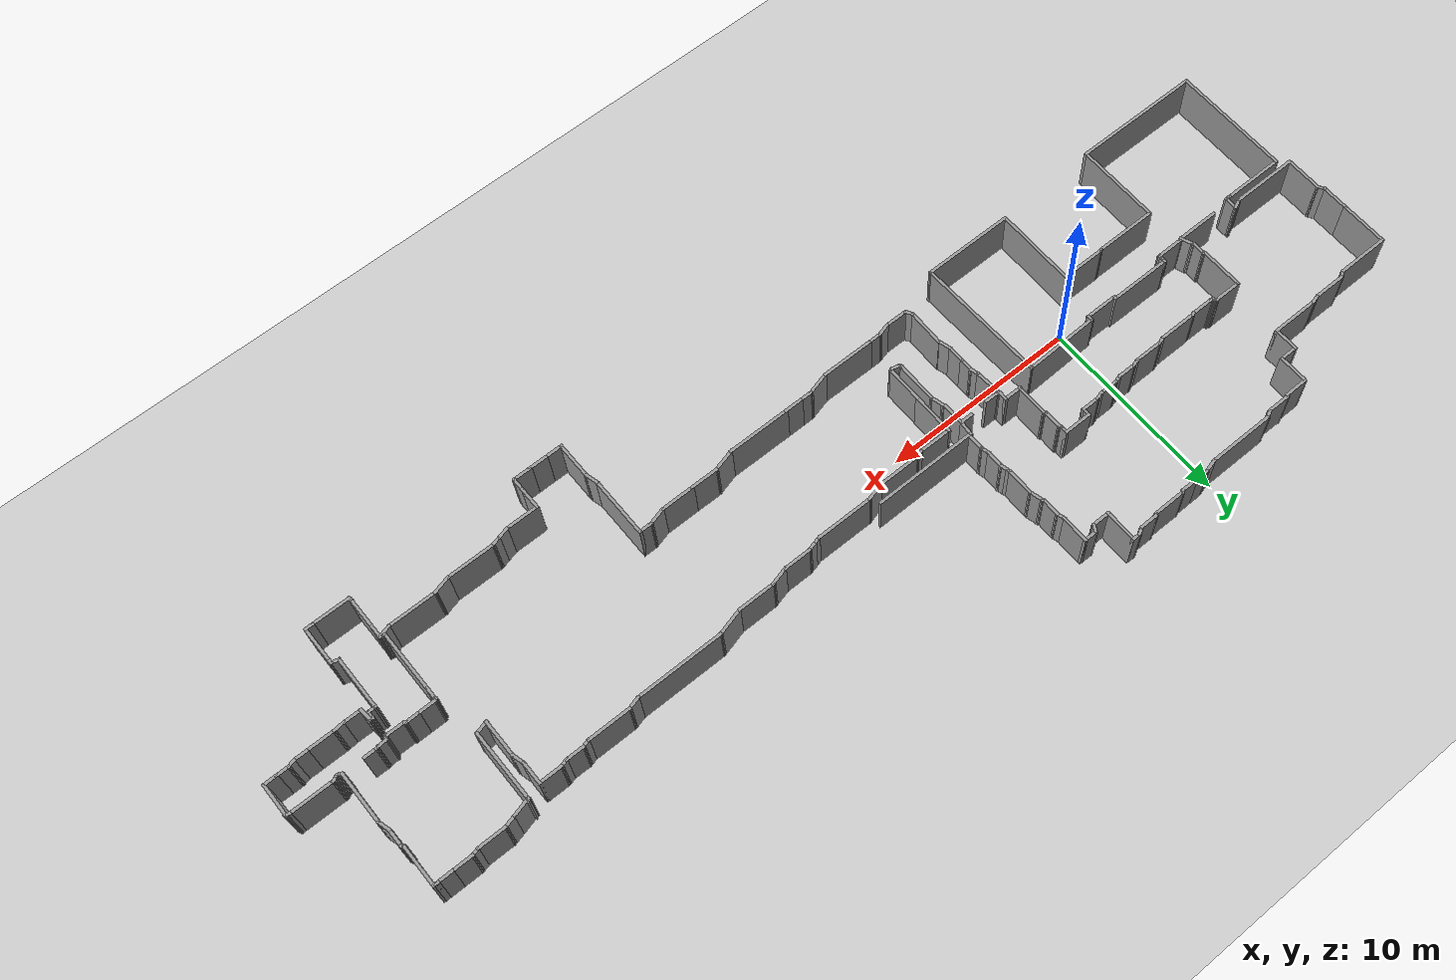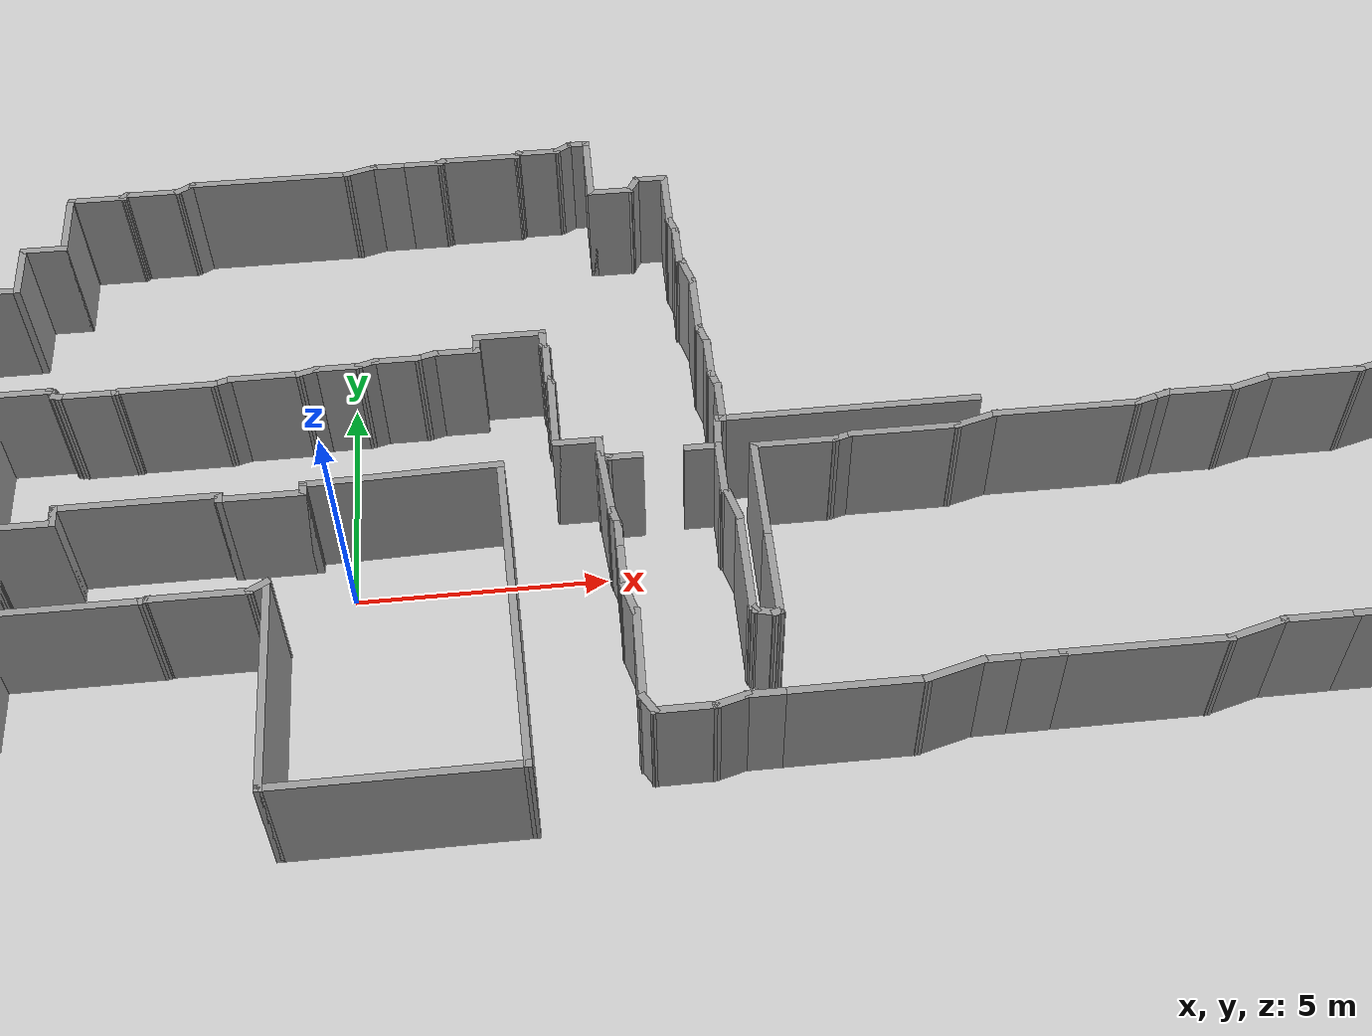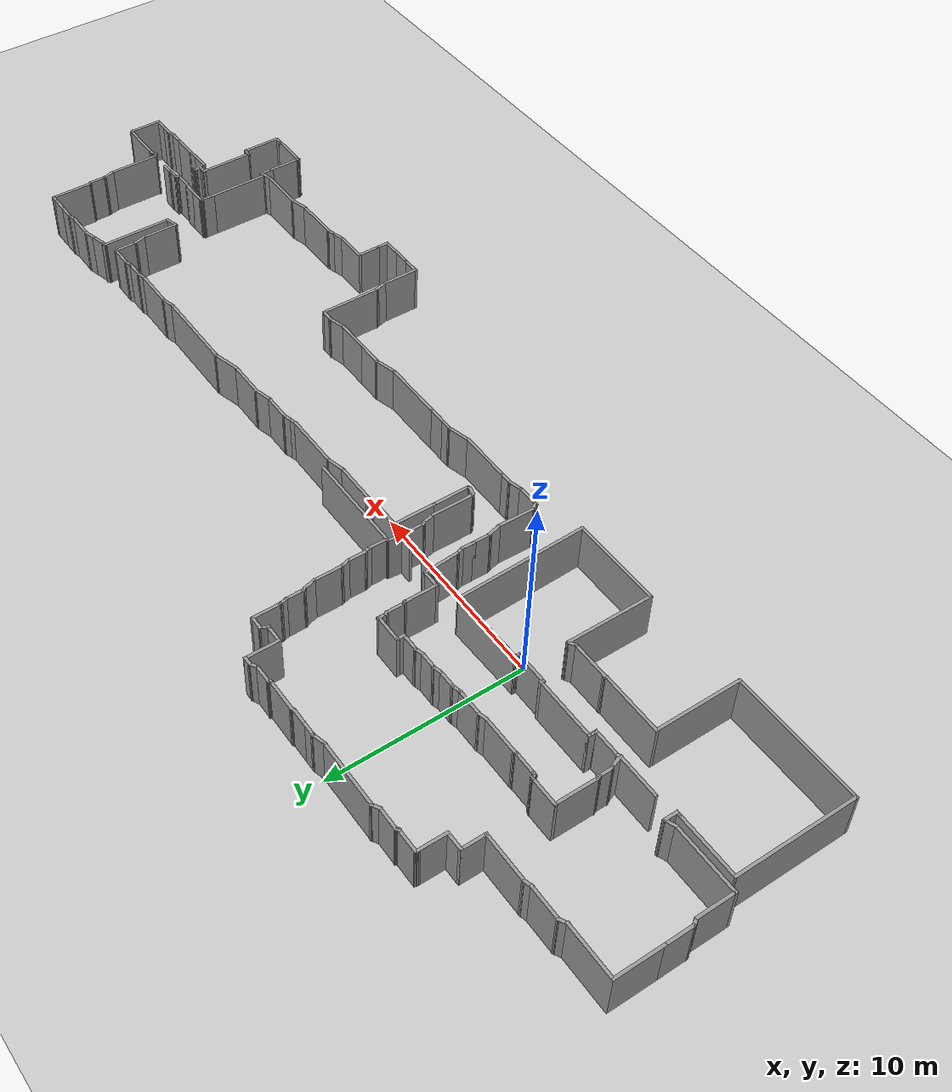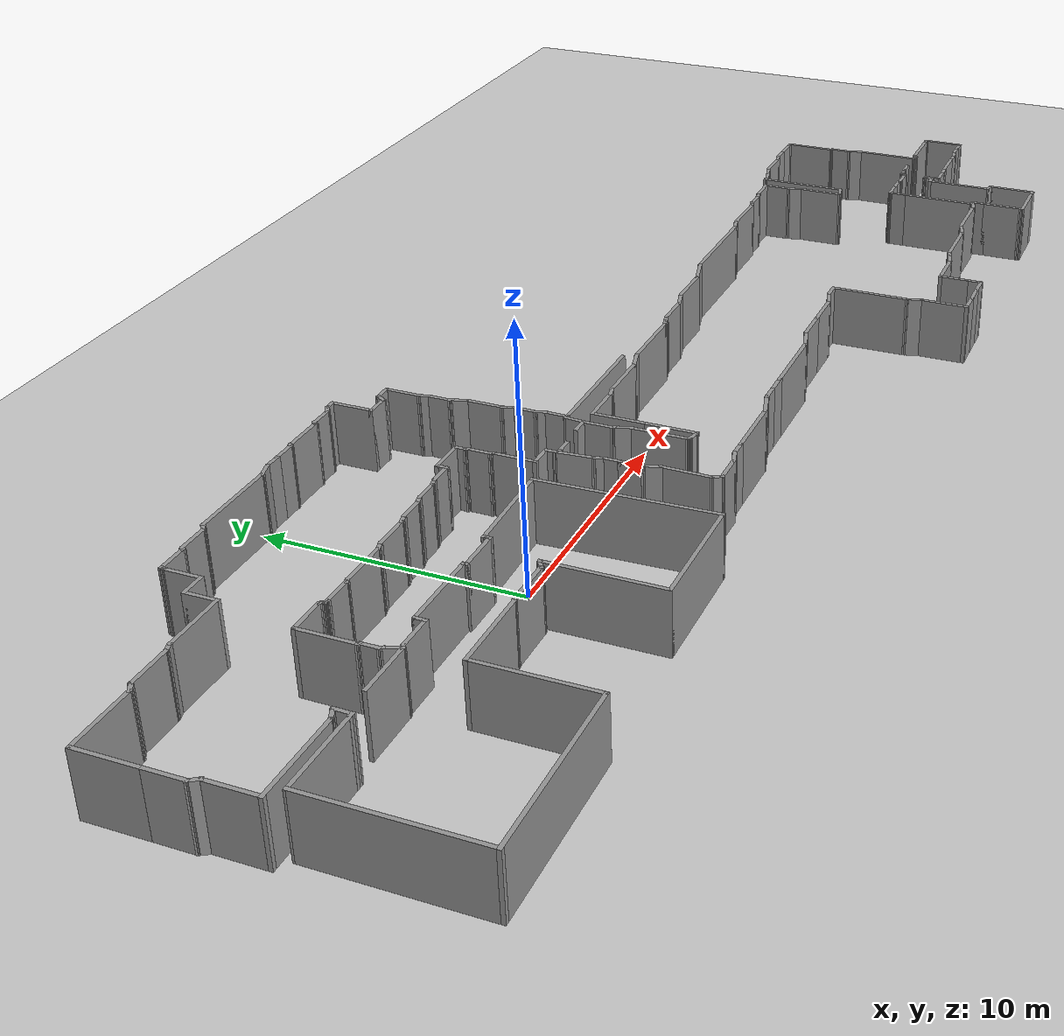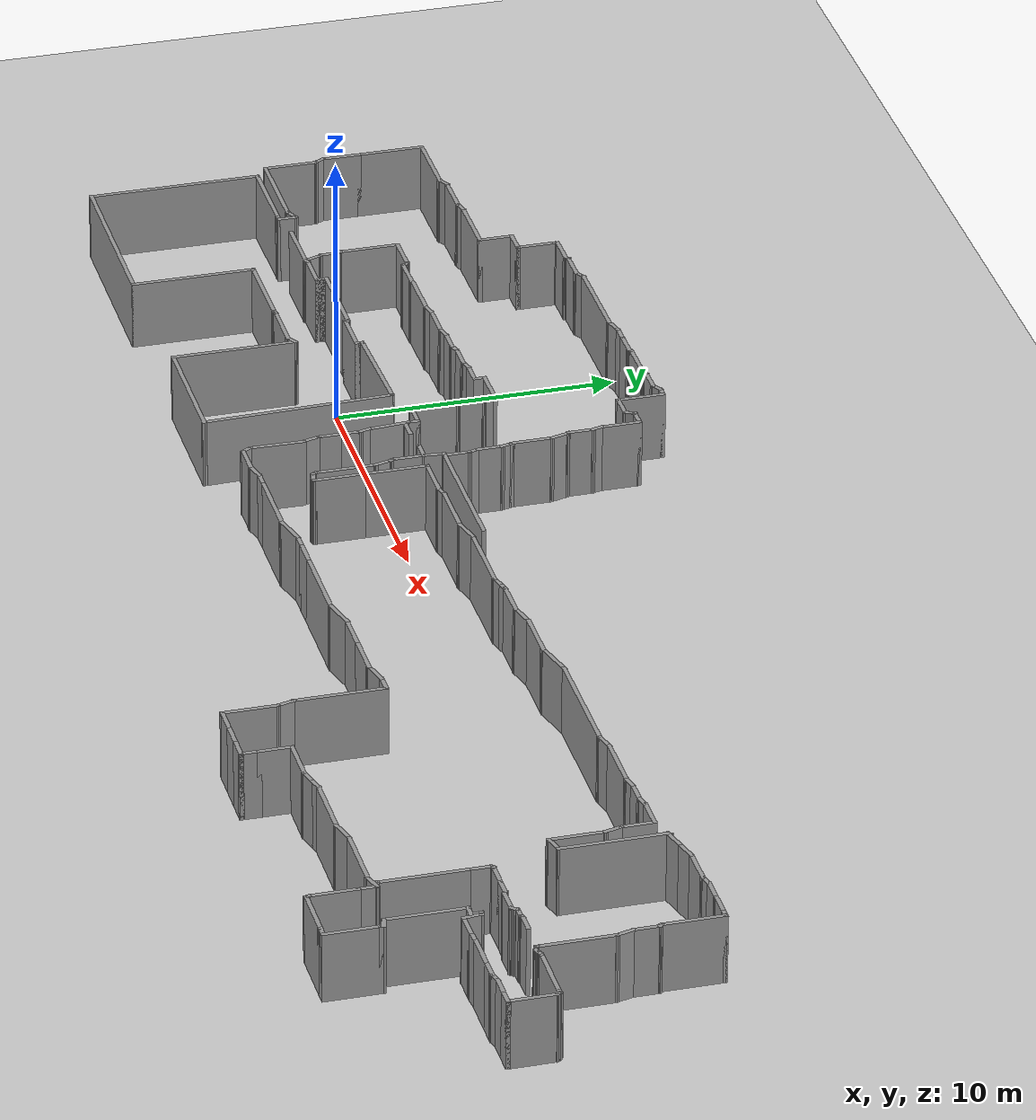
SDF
<sdf version="1.7">
 <world name="default">
  <light name="sun" type="directional">
   <pose>0 0 10 0 -0 0</pose>
   <diffuse>0.8 0.8 0.8 1</diffuse>
   <specular>0.2 0.2 0.2 1</specular>
   <attenuation>
    <range>1000</range>
    <constant>0.9</constant>
    <linear>0.01</linear>
    <quadratic>0.001</quadratic>
   </attenuation>
   <direction>-0.5 0.1 -0.9</direction>
   <spot><inner_angle>0</inner_angle><outer_angle>0</outer_angle><falloff>0</falloff></spot>
  </light>
  <model name="ground_plane">
   <static>1</static>
   <link name="link">
    <collision name="collision">
     <geometry><plane><normal>0 0 1</normal><size>100 100</size></plane></geometry>
     <surface><friction><ode><mu>100</mu><mu2>50</mu2></ode></friction></surface>
    </collision>
    <visual name="visual">
     <cast_shadows>0</cast_shadows>
     <geometry><plane><normal>0 0 1</normal><size>100 100</size></plane></geometry>
     <material>
      <script><uri>file://media/materials/scripts/gazebo.material</uri><name>Gazebo/Grey</name></script>
     </material>
    </visual>
   </link>
  </model>
  <gravity>0 0 -9.8</gravity>
  <magnetic_field>6e-06 2.3e-05 -4.2e-05</magnetic_field>
  <atmosphere type="adiabatic"/>
  <physics type="ode">
   <max_step_size>0.001</max_step_size>
   <real_time_factor>1</real_time_factor>
   <real_time_update_rate>1000</real_time_update_rate>
  </physics>
  <scene><ambient>0.4 0.4 0.4 1</ambient><background>0.7 0.7 0.7 1</background><shadows>1</shadows></scene>
  <spherical_coordinates>
   <surface_model>EARTH_WGS84</surface_model>
   <latitude_deg>0</latitude_deg>
   <longitude_deg>0</longitude_deg>
   <elevation>0</elevation>
   <heading_deg>0</heading_deg>
  </spherical_coordinates>
  <model name="robovisor_env2">
   <pose>13.0565 0.516666 0 0 -0 0</pose>
   <link name="Wall_0">
    <collision name="Wall_0_Collision">
     <geometry><box><size>0.5 0.15 2.5</size></box></geometry>
     <pose>0 0 1.25 0 -0 0</pose>
    </collision>
    <visual name="Wall_0_Visual">
     <pose>0 0 1.25 0 -0 0</pose>
     <geometry><box><size>0.5 0.15 2.5</size></box></geometry>
     <material>
      <script><uri>file://media/materials/scripts/gazebo.material</uri><name>Gazebo/Grey</name></script>
      <ambient>1 1 1 1</ambient>
     </material>
     <meta><layer>0</layer></meta>
    </visual>
    <pose>-18.4525 0.304932 0 0 -0 1.5708</pose>
   </link>
   <link name="Wall_1">
    <collision name="Wall_1_Collision">
     <geometry><box><size>3.25 0.15 2.5</size></box></geometry>
     <pose>0 0 1.25 0 -0 0</pose>
    </collision>
    <visual name="Wall_1_Visual">
     <pose>0 0 1.25 0 -0 0</pose>
     <geometry><box><size>3.25 0.15 2.5</size></box></geometry>
     <material>
      <script><uri>file://media/materials/scripts/gazebo.material</uri><name>Gazebo/Grey</name></script>
      <ambient>1 1 1 1</ambient>
     </material>
     <meta><layer>0</layer></meta>
    </visual>
    <pose>-16.9025 0.479932 0 0 -0 0</pose>
   </link>
   <link name="Wall_101">
    <collision name="Wall_101_Collision">
     <geometry><box><size>0.25 0.15 2.5</size></box></geometry>
     <pose>0 0 1.25 0 -0 0</pose>
    </collision>
    <visual name="Wall_101_Visual">
     <pose>0 0 1.25 0 -0 0</pose>
     <geometry><box><size>0.25 0.15 2.5</size></box></geometry>
     <material>
      <script><uri>file://media/materials/scripts/gazebo.material</uri><name>Gazebo/Grey</name></script>
      <ambient>1 1 1 1</ambient>
     </material>
     <meta><layer>0</layer></meta>
    </visual>
    <pose>-5.62434 1.40609 0 0 -0 3.14159</pose>
   </link>
   <link name="Wall_105">
    <collision name="Wall_105_Collision">
     <geometry><box><size>0.75 0.15 2.5</size></box></geometry>
     <pose>0 0 1.25 0 -0 0</pose>
    </collision>
    <visual name="Wall_105_Visual">
     <pose>0 0 1.25 0 -0 0</pose>
     <geometry><box><size>0.75 0.15 2.5</size></box></geometry>
     <material>
      <script><uri>file://media/materials/scripts/gazebo.material</uri><name>Gazebo/Grey</name></script>
      <ambient>1 1 1 1</ambient>
     </material>
     <meta><layer>0</layer></meta>
    </visual>
    <pose>-6.03532 0.716268 0 0 -0 0</pose>
   </link>
   <link name="Wall_110">
    <collision name="Wall_110_Collision">
     <geometry><box><size>0.842512 0.15 2.5</size></box></geometry>
     <pose>0 0 1.25 0 -0 0</pose>
    </collision>
    <visual name="Wall_110_Visual">
     <pose>0 0 1.25 0 -0 0</pose>
     <geometry><box><size>0.842512 0.15 2.5</size></box></geometry>
     <material>
      <script><uri>file://media/materials/scripts/gazebo.material</uri><name>Gazebo/Grey</name></script>
      <ambient>1 1 1 1</ambient>
     </material>
     <meta><layer>0</layer></meta>
    </visual>
    <pose>-5.70483 1.06118 0 0 -0 1.48262</pose>
   </link>
   <link name="Wall_112">
    <collision name="Wall_112_Collision">
     <geometry><box><size>0.75 0.15 2.5</size></box></geometry>
     <pose>0 0 1.25 0 -0 0</pose>
    </collision>
    <visual name="Wall_112_Visual">
     <pose>0 0 1.25 0 -0 0</pose>
     <geometry><box><size>0.75 0.15 2.5</size></box></geometry>
     <material>
      <script><uri>file://media/materials/scripts/gazebo.material</uri><name>Gazebo/Grey</name></script>
      <ambient>1 1 1 1</ambient>
     </material>
     <meta><layer>0</layer></meta>
    </visual>
    <pose>-7.58545 0.639279 0 0 -0 3.14159</pose>
   </link>
   <link name="Wall_113">
    <collision name="Wall_113_Collision">
     <geometry><box><size>0.25 0.15 2.5</size></box></geometry>
     <pose>0 0 1.25 0 -0 0</pose>
    </collision>
    <visual name="Wall_113_Visual">
     <pose>0 0 1.25 0 -0 0</pose>
     <geometry><box><size>0.25 0.15 2.5</size></box></geometry>
     <material>
      <script><uri>file://media/materials/scripts/gazebo.material</uri><name>Gazebo/Grey</name></script>
      <ambient>1 1 1 1</ambient>
     </material>
     <meta><layer>0</layer></meta>
    </visual>
    <pose>-7.93375 0.65222 0 0 -0 2.87979</pose>
   </link>
   <link name="Wall_114">
    <collision name="Wall_114_Collision">
     <geometry><box><size>0.25 0.15 2.5</size></box></geometry>
     <pose>0 0 1.25 0 -0 0</pose>
    </collision>
    <visual name="Wall_114_Visual">
     <pose>0 0 1.25 0 -0 0</pose>
     <geometry><box><size>0.25 0.15 2.5</size></box></geometry>
     <material>
      <script><uri>file://media/materials/scripts/gazebo.material</uri><name>Gazebo/Grey</name></script>
      <ambient>1 1 1 1</ambient>
     </material>
     <meta><layer>0</layer></meta>
    </visual>
    <pose>-8.00704 0.708463 0 0 -0 2.0944</pose>
   </link>
   <link name="Wall_115">
    <collision name="Wall_115_Collision">
     <geometry><box><size>0.5 0.15 2.5</size></box></geometry>
     <pose>0 0 1.25 0 -0 0</pose>
    </collision>
    <visual name="Wall_115_Visual">
     <pose>0 0 1.25 0 -0 0</pose>
     <geometry><box><size>0.5 0.15 2.5</size></box></geometry>
     <material>
      <script><uri>file://media/materials/scripts/gazebo.material</uri><name>Gazebo/Grey</name></script>
      <ambient>1 1 1 1</ambient>
     </material>
     <meta><layer>0</layer></meta>
    </visual>
    <pose>-8.03204 0.926764 0 0 -0 1.5708</pose>
   </link>
   <link name="Wall_116">
    <collision name="Wall_116_Collision">
     <geometry><box><size>1 0.15 2.5</size></box></geometry>
     <pose>0 0 1.25 0 -0 0</pose>
    </collision>
    <visual name="Wall_116_Visual">
     <pose>0 0 1.25 0 -0 0</pose>
     <geometry><box><size>1 0.15 2.5</size></box></geometry>
     <material>
      <script><uri>file://media/materials/scripts/gazebo.material</uri><name>Gazebo/Grey</name></script>
      <ambient>1 1 1 1</ambient>
     </material>
     <meta><layer>0</layer></meta>
    </visual>
    <pose>-8.45704 1.10176 0 0 -0 3.14159</pose>
   </link>
   <link name="Wall_117">
    <collision name="Wall_117_Collision">
     <geometry><box><size>1.75 0.15 2.5</size></box></geometry>
     <pose>0 0 1.25 0 -0 0</pose>
    </collision>
    <visual name="Wall_117_Visual">
     <pose>0 0 1.25 0 -0 0</pose>
     <geometry><box><size>1.75 0.15 2.5</size></box></geometry>
     <material>
      <script><uri>file://media/materials/scripts/gazebo.material</uri><name>Gazebo/Grey</name></script>
      <ambient>1 1 1 1</ambient>
     </material>
     <meta><layer>0</layer></meta>
    </visual>
    <pose>-8.88204 1.90176 0 0 -0 1.5708</pose>
   </link>
   <link name="Wall_119">
    <collision name="Wall_119_Collision">
     <geometry><box><size>0.25 0.15 2.5</size></box></geometry>
     <pose>0 0 1.25 0 -0 0</pose>
    </collision>
    <visual name="Wall_119_Visual">
     <pose>0 0 1.25 0 -0 0</pose>
     <geometry><box><size>0.25 0.15 2.5</size></box></geometry>
     <material>
      <script><uri>file://media/materials/scripts/gazebo.material</uri><name>Gazebo/Grey</name></script>
      <ambient>1 1 1 1</ambient>
     </material>
     <meta><layer>0</layer></meta>
    </visual>
    <pose>-8.90704 2.74506 0 0 -0 2.0944</pose>
   </link>
   <link name="Wall_120">
    <collision name="Wall_120_Collision">
     <geometry><box><size>1 0.15 2.5</size></box></geometry>
     <pose>0 0 1.25 0 -0 0</pose>
    </collision>
    <visual name="Wall_120_Visual">
     <pose>0 0 1.25 0 -0 0</pose>
     <geometry><box><size>1 0.15 2.5</size></box></geometry>
     <material>
      <script><uri>file://media/materials/scripts/gazebo.material</uri><name>Gazebo/Grey</name></script>
      <ambient>1 1 1 1</ambient>
     </material>
     <meta><layer>0</layer></meta>
    </visual>
    <pose>-8.93204 3.21337 0 0 -0 1.5708</pose>
   </link>
   <link name="Wall_121">
    <collision name="Wall_121_Collision">
     <geometry><box><size>0.25 0.15 2.5</size></box></geometry>
     <pose>0 0 1.25 0 -0 0</pose>
    </collision>
    <visual name="Wall_121_Visual">
     <pose>0 0 1.25 0 -0 0</pose>
     <geometry><box><size>0.25 0.15 2.5</size></box></geometry>
     <material>
      <script><uri>file://media/materials/scripts/gazebo.material</uri><name>Gazebo/Grey</name></script>
      <ambient>1 1 1 1</ambient>
     </material>
     <meta><layer>0</layer></meta>
    </visual>
    <pose>-8.95704 3.68167 0 0 -0 2.0944</pose>
   </link>
   <link name="Wall_122">
    <collision name="Wall_122_Collision">
     <geometry><box><size>0.5 0.15 2.5</size></box></geometry>
     <pose>0 0 1.25 0 -0 0</pose>
    </collision>
    <visual name="Wall_122_Visual">
     <pose>0 0 1.25 0 -0 0</pose>
     <geometry><box><size>0.5 0.15 2.5</size></box></geometry>
     <material>
      <script><uri>file://media/materials/scripts/gazebo.material</uri><name>Gazebo/Grey</name></script>
      <ambient>1 1 1 1</ambient>
     </material>
     <meta><layer>0</layer></meta>
    </visual>
    <pose>-8.98204 3.89997 0 0 -0 1.5708</pose>
   </link>
   <link name="Wall_123">
    <collision name="Wall_123_Collision">
     <geometry><box><size>1.5 0.15 2.5</size></box></geometry>
     <pose>0 0 1.25 0 -0 0</pose>
    </collision>
    <visual name="Wall_123_Visual">
     <pose>0 0 1.25 0 -0 0</pose>
     <geometry><box><size>1.5 0.15 2.5</size></box></geometry>
     <material>
      <script><uri>file://media/materials/scripts/gazebo.material</uri><name>Gazebo/Grey</name></script>
      <ambient>1 1 1 1</ambient>
     </material>
     <meta><layer>0</layer></meta>
    </visual>
    <pose>-9.65704 4.07497 0 0 -0 3.14159</pose>
   </link>
   <link name="Wall_124">
    <collision name="Wall_124_Collision">
     <geometry><box><size>0.5 0.15 2.5</size></box></geometry>
     <pose>0 0 1.25 0 -0 0</pose>
    </collision>
    <visual name="Wall_124_Visual">
     <pose>0 0 1.25 0 -0 0</pose>
     <geometry><box><size>0.5 0.15 2.5</size></box></geometry>
     <material>
      <script><uri>file://media/materials/scripts/gazebo.material</uri><name>Gazebo/Grey</name></script>
      <ambient>1 1 1 1</ambient>
     </material>
     <meta><layer>0</layer></meta>
    </visual>
    <pose>-10.332 3.89997 0 0 -0 -1.5708</pose>
   </link>
   <link name="Wall_126">
    <collision name="Wall_126_Collision">
     <geometry><box><size>1 0.15 2.5</size></box></geometry>
     <pose>0 0 1.25 0 -0 0</pose>
    </collision>
    <visual name="Wall_126_Visual">
     <pose>0 0 1.25 0 -0 0</pose>
     <geometry><box><size>1 0.15 2.5</size></box></geometry>
     <material>
      <script><uri>file://media/materials/scripts/gazebo.material</uri><name>Gazebo/Grey</name></script>
      <ambient>1 1 1 1</ambient>
     </material>
     <meta><layer>0</layer></meta>
    </visual>
    <pose>-10.757 3.72497 0 0 -0 3.14159</pose>
   </link>
   <link name="Wall_127">
    <collision name="Wall_127_Collision">
     <geometry><box><size>0.5 0.15 2.5</size></box></geometry>
     <pose>0 0 1.25 0 -0 0</pose>
    </collision>
    <visual name="Wall_127_Visual">
     <pose>0 0 1.25 0 -0 0</pose>
     <geometry><box><size>0.5 0.15 2.5</size></box></geometry>
     <material>
      <script><uri>file://media/materials/scripts/gazebo.material</uri><name>Gazebo/Grey</name></script>
      <ambient>1 1 1 1</ambient>
     </material>
     <meta><layer>0</layer></meta>
    </visual>
    <pose>-11.3511 3.67968 0 0 -0 -2.87979</pose>
   </link>
   <link name="Wall_128">
    <collision name="Wall_128_Collision">
     <geometry><box><size>1 0.15 2.5</size></box></geometry>
     <pose>0 0 1.25 0 -0 0</pose>
    </collision>
    <visual name="Wall_128_Visual">
     <pose>0 0 1.25 0 -0 0</pose>
     <geometry><box><size>1 0.15 2.5</size></box></geometry>
     <material>
      <script><uri>file://media/materials/scripts/gazebo.material</uri><name>Gazebo/Grey</name></script>
      <ambient>1 1 1 1</ambient>
     </material>
     <meta><layer>0</layer></meta>
    </visual>
    <pose>-11.9451 3.63438 0 0 -0 3.14159</pose>
   </link>
   <link name="Wall_129">
    <collision name="Wall_129_Collision">
     <geometry><box><size>0.5 0.15 2.5</size></box></geometry>
     <pose>0 0 1.25 0 -0 0</pose>
    </collision>
    <visual name="Wall_129_Visual">
     <pose>0 0 1.25 0 -0 0</pose>
     <geometry><box><size>0.5 0.15 2.5</size></box></geometry>
     <material>
      <script><uri>file://media/materials/scripts/gazebo.material</uri><name>Gazebo/Grey</name></script>
      <ambient>1 1 1 1</ambient>
     </material>
     <meta><layer>0</layer></meta>
    </visual>
    <pose>-12.5392 3.58909 0 0 -0 -2.87979</pose>
   </link>
   <link name="Wall_13">
    <collision name="Wall_13_Collision">
     <geometry><box><size>3.92846 0.15 2.5</size></box></geometry>
     <pose>0 0 1.25 0 -0 0</pose>
    </collision>
    <visual name="Wall_13_Visual">
     <pose>0 0 1.25 0 -0 0</pose>
     <geometry><box><size>3.92846 0.15 2.5</size></box></geometry>
     <material>
      <script><uri>file://media/materials/scripts/gazebo.material</uri><name>Gazebo/Grey</name></script>
      <ambient>1 1 1 1</ambient>
     </material>
     <meta><layer>0</layer></meta>
    </visual>
    <pose>-11.8641 0.634129 0 0 -0 -3.1129</pose>
   </link>
   <link name="Wall_130">
    <collision name="Wall_130_Collision">
     <geometry><box><size>1 0.15 2.5</size></box></geometry>
     <pose>0 0 1.25 0 -0 0</pose>
    </collision>
    <visual name="Wall_130_Visual">
     <pose>0 0 1.25 0 -0 0</pose>
     <geometry><box><size>1 0.15 2.5</size></box></geometry>
     <material>
      <script><uri>file://media/materials/scripts/gazebo.material</uri><name>Gazebo/Grey</name></script>
      <ambient>1 1 1 1</ambient>
     </material>
     <meta><layer>0</layer></meta>
    </visual>
    <pose>-13.1332 3.5438 0 0 -0 3.14159</pose>
   </link>
   <link name="Wall_131">
    <collision name="Wall_131_Collision">
     <geometry><box><size>0.5 0.15 2.5</size></box></geometry>
     <pose>0 0 1.25 0 -0 0</pose>
    </collision>
    <visual name="Wall_131_Visual">
     <pose>0 0 1.25 0 -0 0</pose>
     <geometry><box><size>0.5 0.15 2.5</size></box></geometry>
     <material>
      <script><uri>file://media/materials/scripts/gazebo.material</uri><name>Gazebo/Grey</name></script>
      <ambient>1 1 1 1</ambient>
     </material>
     <meta><layer>0</layer></meta>
    </visual>
    <pose>-13.7272 3.4985 0 0 -0 -2.87979</pose>
   </link>
   <link name="Wall_132">
    <collision name="Wall_132_Collision">
     <geometry><box><size>1.5 0.15 2.5</size></box></geometry>
     <pose>0 0 1.25 0 -0 0</pose>
    </collision>
    <visual name="Wall_132_Visual">
     <pose>0 0 1.25 0 -0 0</pose>
     <geometry><box><size>1.5 0.15 2.5</size></box></geometry>
     <material>
      <script><uri>file://media/materials/scripts/gazebo.material</uri><name>Gazebo/Grey</name></script>
      <ambient>1 1 1 1</ambient>
     </material>
     <meta><layer>0</layer></meta>
    </visual>
    <pose>-14.5713 3.45321 0 0 -0 3.14159</pose>
   </link>
   <link name="Wall_133">
    <collision name="Wall_133_Collision">
     <geometry><box><size>0.5 0.15 2.5</size></box></geometry>
     <pose>0 0 1.25 0 -0 0</pose>
    </collision>
    <visual name="Wall_133_Visual">
     <pose>0 0 1.25 0 -0 0</pose>
     <geometry><box><size>0.5 0.15 2.5</size></box></geometry>
     <material>
      <script><uri>file://media/materials/scripts/gazebo.material</uri><name>Gazebo/Grey</name></script>
      <ambient>1 1 1 1</ambient>
     </material>
     <meta><layer>0</layer></meta>
    </visual>
    <pose>-15.4153 3.40792 0 0 -0 -2.87979</pose>
   </link>
   <link name="Wall_134">
    <collision name="Wall_134_Collision">
     <geometry><box><size>2 0.15 2.5</size></box></geometry>
     <pose>0 0 1.25 0 -0 0</pose>
    </collision>
    <visual name="Wall_134_Visual">
     <pose>0 0 1.25 0 -0 0</pose>
     <geometry><box><size>2 0.15 2.5</size></box></geometry>
     <material>
      <script><uri>file://media/materials/scripts/gazebo.material</uri><name>Gazebo/Grey</name></script>
      <ambient>1 1 1 1</ambient>
     </material>
     <meta><layer>0</layer></meta>
    </visual>
    <pose>-16.5093 3.36262 0 0 -0 3.14159</pose>
   </link>
   <link name="Wall_135">
    <collision name="Wall_135_Collision">
     <geometry><box><size>0.25 0.15 2.5</size></box></geometry>
     <pose>0 0 1.25 0 -0 0</pose>
    </collision>
    <visual name="Wall_135_Visual">
     <pose>0 0 1.25 0 -0 0</pose>
     <geometry><box><size>0.25 0.15 2.5</size></box></geometry>
     <material>
      <script><uri>file://media/materials/scripts/gazebo.material</uri><name>Gazebo/Grey</name></script>
      <ambient>1 1 1 1</ambient>
     </material>
     <meta><layer>0</layer></meta>
    </visual>
    <pose>-17.4826 3.34968 0 0 -0 -2.87979</pose>
   </link>
   <link name="Wall_136">
    <collision name="Wall_136_Collision">
     <geometry><box><size>1.25 0.15 2.5</size></box></geometry>
     <pose>0 0 1.25 0 -0 0</pose>
    </collision>
    <visual name="Wall_136_Visual">
     <pose>0 0 1.25 0 -0 0</pose>
     <geometry><box><size>1.25 0.15 2.5</size></box></geometry>
     <material>
      <script><uri>file://media/materials/scripts/gazebo.material</uri><name>Gazebo/Grey</name></script>
      <ambient>1 1 1 1</ambient>
     </material>
     <meta><layer>0</layer></meta>
    </visual>
    <pose>-18.0809 3.33674 0 0 -0 3.14159</pose>
   </link>
   <link name="Wall_137">
    <collision name="Wall_137_Collision">
     <geometry><box><size>0.25 0.15 2.5</size></box></geometry>
     <pose>0 0 1.25 0 -0 0</pose>
    </collision>
    <visual name="Wall_137_Visual">
     <pose>0 0 1.25 0 -0 0</pose>
     <geometry><box><size>0.25 0.15 2.5</size></box></geometry>
     <material>
      <script><uri>file://media/materials/scripts/gazebo.material</uri><name>Gazebo/Grey</name></script>
      <ambient>1 1 1 1</ambient>
     </material>
     <meta><layer>0</layer></meta>
    </visual>
    <pose>-18.6792 3.34968 0 0 -0 2.87979</pose>
   </link>
   <link name="Wall_138">
    <collision name="Wall_138_Collision">
     <geometry><box><size>0.25 0.15 2.5</size></box></geometry>
     <pose>0 0 1.25 0 -0 0</pose>
    </collision>
    <visual name="Wall_138_Visual">
     <pose>0 0 1.25 0 -0 0</pose>
     <geometry><box><size>0.25 0.15 2.5</size></box></geometry>
     <material>
      <script><uri>file://media/materials/scripts/gazebo.material</uri><name>Gazebo/Grey</name></script>
      <ambient>1 1 1 1</ambient>
     </material>
     <meta><layer>0</layer></meta>
    </visual>
    <pose>-18.7405 3.41092 0 0 -0 1.8326</pose>
   </link>
   <link name="Wall_139">
    <collision name="Wall_139_Collision">
     <geometry><box><size>0.25 0.15 2.5</size></box></geometry>
     <pose>0 0 1.25 0 -0 0</pose>
    </collision>
    <visual name="Wall_139_Visual">
     <pose>0 0 1.25 0 -0 0</pose>
     <geometry><box><size>0.25 0.15 2.5</size></box></geometry>
     <material>
      <script><uri>file://media/materials/scripts/gazebo.material</uri><name>Gazebo/Grey</name></script>
      <ambient>1 1 1 1</ambient>
     </material>
     <meta><layer>0</layer></meta>
    </visual>
    <pose>-18.7967 3.48421 0 0 -0 2.61799</pose>
   </link>
   <link name="Wall_140">
    <collision name="Wall_140_Collision">
     <geometry><box><size>1.5 0.15 2.5</size></box></geometry>
     <pose>0 0 1.25 0 -0 0</pose>
    </collision>
    <visual name="Wall_140_Visual">
     <pose>0 0 1.25 0 -0 0</pose>
     <geometry><box><size>1.5 0.15 2.5</size></box></geometry>
     <material>
      <script><uri>file://media/materials/scripts/gazebo.material</uri><name>Gazebo/Grey</name></script>
      <ambient>1 1 1 1</ambient>
     </material>
     <meta><layer>0</layer></meta>
    </visual>
    <pose>-19.515 3.50922 0 0 -0 3.14159</pose>
   </link>
   <link name="Wall_141">
    <collision name="Wall_141_Collision">
     <geometry><box><size>2.25 0.15 2.5</size></box></geometry>
     <pose>0 0 1.25 0 -0 0</pose>
    </collision>
    <visual name="Wall_141_Visual">
     <pose>0 0 1.25 0 -0 0</pose>
     <geometry><box><size>2.25 0.15 2.5</size></box></geometry>
     <material>
      <script><uri>file://media/materials/scripts/gazebo.material</uri><name>Gazebo/Grey</name></script>
      <ambient>1 1 1 1</ambient>
     </material>
     <meta><layer>0</layer></meta>
    </visual>
    <pose>-20.19 2.45921 0 0 -0 -1.5708</pose>
   </link>
   <link name="Wall_144">
    <collision name="Wall_144_Collision">
     <geometry><box><size>0.25 0.15 2.5</size></box></geometry>
     <pose>0 0 1.25 0 -0 0</pose>
    </collision>
    <visual name="Wall_144_Visual">
     <pose>0 0 1.25 0 -0 0</pose>
     <geometry><box><size>0.25 0.15 2.5</size></box></geometry>
     <material>
      <script><uri>file://media/materials/scripts/gazebo.material</uri><name>Gazebo/Grey</name></script>
      <ambient>1 1 1 1</ambient>
     </material>
     <meta><layer>0</layer></meta>
    </visual>
    <pose>-20.165 1.36591 0 0 -0 -1.0472</pose>
   </link>
   <link name="Wall_145">
    <collision name="Wall_145_Collision">
     <geometry><box><size>0.75 0.15 2.5</size></box></geometry>
     <pose>0 0 1.25 0 -0 0</pose>
    </collision>
    <visual name="Wall_145_Visual">
     <pose>0 0 1.25 0 -0 0</pose>
     <geometry><box><size>0.75 0.15 2.5</size></box></geometry>
     <material>
      <script><uri>file://media/materials/scripts/gazebo.material</uri><name>Gazebo/Grey</name></script>
      <ambient>1 1 1 1</ambient>
     </material>
     <meta><layer>0</layer></meta>
    </visual>
    <pose>-20.14 1.02261 0 0 -0 -1.5708</pose>
   </link>
   <link name="Wall_146">
    <collision name="Wall_146_Collision">
     <geometry><box><size>0.25 0.15 2.5</size></box></geometry>
     <pose>0 0 1.25 0 -0 0</pose>
    </collision>
    <visual name="Wall_146_Visual">
     <pose>0 0 1.25 0 -0 0</pose>
     <geometry><box><size>0.25 0.15 2.5</size></box></geometry>
     <material>
      <script><uri>file://media/materials/scripts/gazebo.material</uri><name>Gazebo/Grey</name></script>
      <ambient>1 1 1 1</ambient>
     </material>
     <meta><layer>0</layer></meta>
    </visual>
    <pose>-20.115 0.679311 0 0 -0 -1.0472</pose>
   </link>
   <link name="Wall_147">
    <collision name="Wall_147_Collision">
     <geometry><box><size>0.741245 0.15 2.5</size></box></geometry>
     <pose>0 0 1.25 0 -0 0</pose>
    </collision>
    <visual name="Wall_147_Visual">
     <pose>0 0 1.25 0 -0 0</pose>
     <geometry><box><size>0.741245 0.15 2.5</size></box></geometry>
     <material>
      <script><uri>file://media/materials/scripts/gazebo.material</uri><name>Gazebo/Grey</name></script>
      <ambient>1 1 1 1</ambient>
     </material>
     <meta><layer>0</layer></meta>
    </visual>
    <pose>-19.9896 0.357971 0 0 -0 -1.22416</pose>
   </link>
   <link name="Wall_151">
    <collision name="Wall_151_Collision">
     <geometry><box><size>1.25 0.15 2.5</size></box></geometry>
     <pose>0 0 1.25 0 -0 0</pose>
    </collision>
    <visual name="Wall_151_Visual">
     <pose>0 0 1.25 0 -0 0</pose>
     <geometry><box><size>1.25 0.15 2.5</size></box></geometry>
     <material>
      <script><uri>file://media/materials/scripts/gazebo.material</uri><name>Gazebo/Grey</name></script>
      <ambient>1 1 1 1</ambient>
     </material>
     <meta><layer>0</layer></meta>
    </visual>
    <pose>-5.73532 0.166268 0 0 -0 -1.5708</pose>
   </link>
   <link name="Wall_152">
    <collision name="Wall_152_Collision">
     <geometry><box><size>0.25 0.15 2.5</size></box></geometry>
     <pose>0 0 1.25 0 -0 0</pose>
    </collision>
    <visual name="Wall_152_Visual">
     <pose>0 0 1.25 0 -0 0</pose>
     <geometry><box><size>0.25 0.15 2.5</size></box></geometry>
     <material>
      <script><uri>file://media/materials/scripts/gazebo.material</uri><name>Gazebo/Grey</name></script>
      <ambient>1 1 1 1</ambient>
     </material>
     <meta><layer>0</layer></meta>
    </visual>
    <pose>-5.71032 -0.427033 0 0 -0 -1.0472</pose>
   </link>
   <link name="Wall_153">
    <collision name="Wall_153_Collision">
     <geometry><box><size>0.75 0.15 2.5</size></box></geometry>
     <pose>0 0 1.25 0 -0 0</pose>
    </collision>
    <visual name="Wall_153_Visual">
     <pose>0 0 1.25 0 -0 0</pose>
     <geometry><box><size>0.75 0.15 2.5</size></box></geometry>
     <material>
      <script><uri>file://media/materials/scripts/gazebo.material</uri><name>Gazebo/Grey</name></script>
      <ambient>1 1 1 1</ambient>
     </material>
     <meta><layer>0</layer></meta>
    </visual>
    <pose>-5.60768 -0.760112 0 0 -0 -1.309</pose>
   </link>
   <link name="Wall_154">
    <collision name="Wall_154_Collision">
     <geometry><box><size>2.25 0.15 2.5</size></box></geometry>
     <pose>0 0 1.25 0 -0 0</pose>
    </collision>
    <visual name="Wall_154_Visual">
     <pose>0 0 1.25 0 -0 0</pose>
     <geometry><box><size>2.25 0.15 2.5</size></box></geometry>
     <material>
      <script><uri>file://media/materials/scripts/gazebo.material</uri><name>Gazebo/Grey</name></script>
      <ambient>1 1 1 1</ambient>
     </material>
     <meta><layer>0</layer></meta>
    </visual>
    <pose>-5.53003 -2.09989 0 0 -0 -1.5708</pose>
   </link>
   <link name="Wall_155">
    <collision name="Wall_155_Collision">
     <geometry><box><size>0.25 0.15 2.5</size></box></geometry>
     <pose>0 0 1.25 0 -0 0</pose>
    </collision>
    <visual name="Wall_155_Visual">
     <pose>0 0 1.25 0 -0 0</pose>
     <geometry><box><size>0.25 0.15 2.5</size></box></geometry>
     <material>
      <script><uri>file://media/materials/scripts/gazebo.material</uri><name>Gazebo/Grey</name></script>
      <ambient>1 1 1 1</ambient>
     </material>
     <meta><layer>0</layer></meta>
    </visual>
    <pose>-5.50503 -3.19319 0 0 -0 -1.0472</pose>
   </link>
   <link name="Wall_156">
    <collision name="Wall_156_Collision">
     <geometry><box><size>0.5 0.15 2.5</size></box></geometry>
     <pose>0 0 1.25 0 -0 0</pose>
    </collision>
    <visual name="Wall_156_Visual">
     <pose>0 0 1.25 0 -0 0</pose>
     <geometry><box><size>0.5 0.15 2.5</size></box></geometry>
     <material>
      <script><uri>file://media/materials/scripts/gazebo.material</uri><name>Gazebo/Grey</name></script>
      <ambient>1 1 1 1</ambient>
     </material>
     <meta><layer>0</layer></meta>
    </visual>
    <pose>-5.311 -3.28179 0 0 -0 -0.261799</pose>
   </link>
   <link name="Wall_157">
    <collision name="Wall_157_Collision">
     <geometry><box><size>0.25 0.15 2.5</size></box></geometry>
     <pose>0 0 1.25 0 -0 0</pose>
    </collision>
    <visual name="Wall_157_Visual">
     <pose>0 0 1.25 0 -0 0</pose>
     <geometry><box><size>0.25 0.15 2.5</size></box></geometry>
     <material>
      <script><uri>file://media/materials/scripts/gazebo.material</uri><name>Gazebo/Grey</name></script>
      <ambient>1 1 1 1</ambient>
     </material>
     <meta><layer>0</layer></meta>
    </visual>
    <pose>-5.09366 -3.31414 0 0 -0 0.261799</pose>
   </link>
   <link name="Wall_158">
    <collision name="Wall_158_Collision">
     <geometry><box><size>0.15 0.15 2.5</size></box></geometry>
     <pose>0 0 1.25 0 -0 0</pose>
    </collision>
    <visual name="Wall_158_Visual">
     <pose>0 0 1.25 0 -0 0</pose>
     <geometry><box><size>0.15 0.15 2.5</size></box></geometry>
     <material>
      <script><uri>file://media/materials/scripts/gazebo.material</uri><name>Gazebo/Grey</name></script>
      <ambient>1 1 1 1</ambient>
     </material>
     <meta><layer>0</layer></meta>
    </visual>
    <pose>-5.04537 -3.3012 0 0 -0 0</pose>
   </link>
   <link name="Wall_159">
    <collision name="Wall_159_Collision">
     <geometry><box><size>0.15 0.15 2.5</size></box></geometry>
     <pose>0 0 1.25 0 -0 0</pose>
    </collision>
    <visual name="Wall_159_Visual">
     <pose>0 0 1.25 0 -0 0</pose>
     <geometry><box><size>0.15 0.15 2.5</size></box></geometry>
     <material>
      <script><uri>file://media/materials/scripts/gazebo.material</uri><name>Gazebo/Grey</name></script>
      <ambient>1 1 1 1</ambient>
     </material>
     <meta><layer>0</layer></meta>
    </visual>
    <pose>-5.04537 -3.3012 0 0 -0 0</pose>
   </link>
   <link name="Wall_16">
    <collision name="Wall_16_Collision">
     <geometry><box><size>4.5 0.15 2.5</size></box></geometry>
     <pose>0 0 1.25 0 -0 0</pose>
    </collision>
    <visual name="Wall_16_Visual">
     <pose>0 0 1.25 0 -0 0</pose>
     <geometry><box><size>4.5 0.15 2.5</size></box></geometry>
     <material>
      <script><uri>file://media/materials/scripts/gazebo.material</uri><name>Gazebo/Grey</name></script>
      <ambient>1 1 1 1</ambient>
     </material>
     <meta><layer>0</layer></meta>
    </visual>
    <pose>-14.3741 -3.83787 0 0 -0 -1.5708</pose>
   </link>
   <link name="Wall_160">
    <collision name="Wall_160_Collision">
     <geometry><box><size>2 0.15 2.5</size></box></geometry>
     <pose>0 0 1.25 0 -0 0</pose>
    </collision>
    <visual name="Wall_160_Visual">
     <pose>0 0 1.25 0 -0 0</pose>
     <geometry><box><size>2 0.15 2.5</size></box></geometry>
     <material>
      <script><uri>file://media/materials/scripts/gazebo.material</uri><name>Gazebo/Grey</name></script>
      <ambient>1 1 1 1</ambient>
     </material>
     <meta><layer>0</layer></meta>
    </visual>
    <pose>-5.04537 -2.3762 0 0 -0 1.5708</pose>
   </link>
   <link name="Wall_161">
    <collision name="Wall_161_Collision">
     <geometry><box><size>2.25 0.15 2.5</size></box></geometry>
     <pose>0 0 1.25 0 -0 0</pose>
    </collision>
    <visual name="Wall_161_Visual">
     <pose>0 0 1.25 0 -0 0</pose>
     <geometry><box><size>2.25 0.15 2.5</size></box></geometry>
     <material>
      <script><uri>file://media/materials/scripts/gazebo.material</uri><name>Gazebo/Grey</name></script>
      <ambient>1 1 1 1</ambient>
     </material>
     <meta><layer>0</layer></meta>
    </visual>
    <pose>-5.04537 -0.401197 0 0 -0 1.5708</pose>
   </link>
   <link name="Wall_162">
    <collision name="Wall_162_Collision">
     <geometry><box><size>1.75 0.15 2.5</size></box></geometry>
     <pose>0 0 1.25 0 -0 0</pose>
    </collision>
    <visual name="Wall_162_Visual">
     <pose>0 0 1.25 0 -0 0</pose>
     <geometry><box><size>1.75 0.15 2.5</size></box></geometry>
     <material>
      <script><uri>file://media/materials/scripts/gazebo.material</uri><name>Gazebo/Grey</name></script>
      <ambient>1 1 1 1</ambient>
     </material>
     <meta><layer>0</layer></meta>
    </visual>
    <pose>-4.24536 0.648803 0 0 -0 0</pose>
   </link>
   <link name="Wall_163">
    <collision name="Wall_163_Collision">
     <geometry><box><size>0.5 0.15 2.5</size></box></geometry>
     <pose>0 0 1.25 0 -0 0</pose>
    </collision>
    <visual name="Wall_163_Visual">
     <pose>0 0 1.25 0 -0 0</pose>
     <geometry><box><size>0.5 0.15 2.5</size></box></geometry>
     <material>
      <script><uri>file://media/materials/scripts/gazebo.material</uri><name>Gazebo/Grey</name></script>
      <ambient>1 1 1 1</ambient>
     </material>
     <meta><layer>0</layer></meta>
    </visual>
    <pose>-3.27633 0.694096 0 0 -0 0.261799</pose>
   </link>
   <link name="Wall_164">
    <collision name="Wall_164_Collision">
     <geometry><box><size>2.25 0.15 2.5</size></box></geometry>
     <pose>0 0 1.25 0 -0 0</pose>
    </collision>
    <visual name="Wall_164_Visual">
     <pose>0 0 1.25 0 -0 0</pose>
     <geometry><box><size>2.25 0.15 2.5</size></box></geometry>
     <material>
      <script><uri>file://media/materials/scripts/gazebo.material</uri><name>Gazebo/Grey</name></script>
      <ambient>1 1 1 1</ambient>
     </material>
     <meta><layer>0</layer></meta>
    </visual>
    <pose>-2.05729 0.73939 0 0 -0 0</pose>
   </link>
   <link name="Wall_165">
    <collision name="Wall_165_Collision">
     <geometry><box><size>1 0.15 2.5</size></box></geometry>
     <pose>0 0 1.25 0 -0 0</pose>
    </collision>
    <visual name="Wall_165_Visual">
     <pose>0 0 1.25 0 -0 0</pose>
     <geometry><box><size>1 0.15 2.5</size></box></geometry>
     <material>
      <script><uri>file://media/materials/scripts/gazebo.material</uri><name>Gazebo/Grey</name></script>
      <ambient>1 1 1 1</ambient>
     </material>
     <meta><layer>0</layer></meta>
    </visual>
    <pose>-0.596773 0.849388 0 0 -0 0.261799</pose>
   </link>
   <link name="Wall_166">
    <collision name="Wall_166_Collision">
     <geometry><box><size>3 0.15 2.5</size></box></geometry>
     <pose>0 0 1.25 0 -0 0</pose>
    </collision>
    <visual name="Wall_166_Visual">
     <pose>0 0 1.25 0 -0 0</pose>
     <geometry><box><size>3 0.15 2.5</size></box></geometry>
     <material>
      <script><uri>file://media/materials/scripts/gazebo.material</uri><name>Gazebo/Grey</name></script>
      <ambient>1 1 1 1</ambient>
     </material>
     <meta><layer>0</layer></meta>
    </visual>
    <pose>1.23875 0.959386 0 0 -0 0</pose>
   </link>
   <link name="Wall_167">
    <collision name="Wall_167_Collision">
     <geometry><box><size>0.5 0.15 2.5</size></box></geometry>
     <pose>0 0 1.25 0 -0 0</pose>
    </collision>
    <visual name="Wall_167_Visual">
     <pose>0 0 1.25 0 -0 0</pose>
     <geometry><box><size>0.5 0.15 2.5</size></box></geometry>
     <material>
      <script><uri>file://media/materials/scripts/gazebo.material</uri><name>Gazebo/Grey</name></script>
      <ambient>1 1 1 1</ambient>
     </material>
     <meta><layer>0</layer></meta>
    </visual>
    <pose>2.83278 1.00468 0 0 -0 0.261799</pose>
   </link>
   <link name="Wall_168">
    <collision name="Wall_168_Collision">
     <geometry><box><size>0.5 0.15 2.5</size></box></geometry>
     <pose>0 0 1.25 0 -0 0</pose>
    </collision>
    <visual name="Wall_168_Visual">
     <pose>0 0 1.25 0 -0 0</pose>
     <geometry><box><size>0.5 0.15 2.5</size></box></geometry>
     <material>
      <script><uri>file://media/materials/scripts/gazebo.material</uri><name>Gazebo/Grey</name></script>
      <ambient>1 1 1 1</ambient>
     </material>
     <meta><layer>0</layer></meta>
    </visual>
    <pose>3.17086 1.09527 0 0 -0 0.261799</pose>
   </link>
   <link name="Wall_169">
    <collision name="Wall_169_Collision">
     <geometry><box><size>1.5 0.15 2.5</size></box></geometry>
     <pose>0 0 1.25 0 -0 0</pose>
    </collision>
    <visual name="Wall_169_Visual">
     <pose>0 0 1.25 0 -0 0</pose>
     <geometry><box><size>1.5 0.15 2.5</size></box></geometry>
     <material>
      <script><uri>file://media/materials/scripts/gazebo.material</uri><name>Gazebo/Grey</name></script>
      <ambient>1 1 1 1</ambient>
     </material>
     <meta><layer>0</layer></meta>
    </visual>
    <pose>4.01489 1.14056 0 0 -0 0</pose>
   </link>
   <link name="Wall_17">
    <collision name="Wall_17_Collision">
     <geometry><box><size>4.75 0.15 2.5</size></box></geometry>
     <pose>0 0 1.25 0 -0 0</pose>
    </collision>
    <visual name="Wall_17_Visual">
     <pose>0 0 1.25 0 -0 0</pose>
     <geometry><box><size>4.75 0.15 2.5</size></box></geometry>
     <material>
      <script><uri>file://media/materials/scripts/gazebo.material</uri><name>Gazebo/Grey</name></script>
      <ambient>1 1 1 1</ambient>
     </material>
     <meta><layer>0</layer></meta>
    </visual>
    <pose>-12.0741 -6.01287 0 0 -0 0</pose>
   </link>
   <link name="Wall_171">
    <collision name="Wall_171_Collision">
     <geometry><box><size>1 0.15 2.5</size></box></geometry>
     <pose>0 0 1.25 0 -0 0</pose>
    </collision>
    <visual name="Wall_171_Visual">
     <pose>0 0 1.25 0 -0 0</pose>
     <geometry><box><size>1 0.15 2.5</size></box></geometry>
     <material>
      <script><uri>file://media/materials/scripts/gazebo.material</uri><name>Gazebo/Grey</name></script>
      <ambient>1 1 1 1</ambient>
     </material>
     <meta><layer>0</layer></meta>
    </visual>
    <pose>5.10041 1.25056 0 0 -0 0.261799</pose>
   </link>
   <link name="Wall_172">
    <collision name="Wall_172_Collision">
     <geometry><box><size>2 0.15 2.5</size></box></geometry>
     <pose>0 0 1.25 0 -0 0</pose>
    </collision>
    <visual name="Wall_172_Visual">
     <pose>0 0 1.25 0 -0 0</pose>
     <geometry><box><size>2 0.15 2.5</size></box></geometry>
     <material>
      <script><uri>file://media/materials/scripts/gazebo.material</uri><name>Gazebo/Grey</name></script>
      <ambient>1 1 1 1</ambient>
     </material>
     <meta><layer>0</layer></meta>
    </visual>
    <pose>6.43593 1.36055 0 0 -0 0</pose>
   </link>
   <link name="Wall_173">
    <collision name="Wall_173_Collision">
     <geometry><box><size>1.5 0.15 2.5</size></box></geometry>
     <pose>0 0 1.25 0 -0 0</pose>
    </collision>
    <visual name="Wall_173_Visual">
     <pose>0 0 1.25 0 -0 0</pose>
     <geometry><box><size>1.5 0.15 2.5</size></box></geometry>
     <material>
      <script><uri>file://media/materials/scripts/gazebo.material</uri><name>Gazebo/Grey</name></script>
      <ambient>1 1 1 1</ambient>
     </material>
     <meta><layer>0</layer></meta>
    </visual>
    <pose>8.01293 1.53526 0 0 -0 0.261799</pose>
   </link>
   <link name="Wall_174">
    <collision name="Wall_174_Collision">
     <geometry><box><size>4.5 0.15 2.5</size></box></geometry>
     <pose>0 0 1.25 0 -0 0</pose>
    </collision>
    <visual name="Wall_174_Visual">
     <pose>0 0 1.25 0 -0 0</pose>
     <geometry><box><size>4.5 0.15 2.5</size></box></geometry>
     <material>
      <script><uri>file://media/materials/scripts/gazebo.material</uri><name>Gazebo/Grey</name></script>
      <ambient>1 1 1 1</ambient>
     </material>
     <meta><layer>0</layer></meta>
    </visual>
    <pose>10.8399 1.70996 0 0 -0 0</pose>
   </link>
   <link name="Wall_175">
    <collision name="Wall_175_Collision">
     <geometry><box><size>0.75 0.15 2.5</size></box></geometry>
     <pose>0 0 1.25 0 -0 0</pose>
    </collision>
    <visual name="Wall_175_Visual">
     <pose>0 0 1.25 0 -0 0</pose>
     <geometry><box><size>0.75 0.15 2.5</size></box></geometry>
     <material>
      <script><uri>file://media/materials/scripts/gazebo.material</uri><name>Gazebo/Grey</name></script>
      <ambient>1 1 1 1</ambient>
     </material>
     <meta><layer>0</layer></meta>
    </visual>
    <pose>13.3047 1.78761 0 0 -0 0.261799</pose>
   </link>
   <link name="Wall_176">
    <collision name="Wall_176_Collision">
     <geometry><box><size>2.25 0.15 2.5</size></box></geometry>
     <pose>0 0 1.25 0 -0 0</pose>
    </collision>
    <visual name="Wall_176_Visual">
     <pose>0 0 1.25 0 -0 0</pose>
     <geometry><box><size>2.25 0.15 2.5</size></box></geometry>
     <material>
      <script><uri>file://media/materials/scripts/gazebo.material</uri><name>Gazebo/Grey</name></script>
      <ambient>1 1 1 1</ambient>
     </material>
     <meta><layer>0</layer></meta>
    </visual>
    <pose>14.6445 1.86525 0 0 -0 0</pose>
   </link>
   <link name="Wall_177">
    <collision name="Wall_177_Collision">
     <geometry><box><size>0.5 0.15 2.5</size></box></geometry>
     <pose>0 0 1.25 0 -0 0</pose>
    </collision>
    <visual name="Wall_177_Visual">
     <pose>0 0 1.25 0 -0 0</pose>
     <geometry><box><size>0.5 0.15 2.5</size></box></geometry>
     <material>
      <script><uri>file://media/materials/scripts/gazebo.material</uri><name>Gazebo/Grey</name></script>
      <ambient>1 1 1 1</ambient>
     </material>
     <meta><layer>0</layer></meta>
    </visual>
    <pose>15.8635 1.91055 0 0 -0 0.261799</pose>
   </link>
   <link name="Wall_178">
    <collision name="Wall_178_Collision">
     <geometry><box><size>1 0.15 2.5</size></box></geometry>
     <pose>0 0 1.25 0 -0 0</pose>
    </collision>
    <visual name="Wall_178_Visual">
     <pose>0 0 1.25 0 -0 0</pose>
     <geometry><box><size>1 0.15 2.5</size></box></geometry>
     <material>
      <script><uri>file://media/materials/scripts/gazebo.material</uri><name>Gazebo/Grey</name></script>
      <ambient>1 1 1 1</ambient>
     </material>
     <meta><layer>0</layer></meta>
    </visual>
    <pose>16.4576 1.95584 0 0 -0 0</pose>
   </link>
   <link name="Wall_179">
    <collision name="Wall_179_Collision">
     <geometry><box><size>0.5 0.15 2.5</size></box></geometry>
     <pose>0 0 1.25 0 -0 0</pose>
    </collision>
    <visual name="Wall_179_Visual">
     <pose>0 0 1.25 0 -0 0</pose>
     <geometry><box><size>0.5 0.15 2.5</size></box></geometry>
     <material>
      <script><uri>file://media/materials/scripts/gazebo.material</uri><name>Gazebo/Grey</name></script>
      <ambient>1 1 1 1</ambient>
     </material>
     <meta><layer>0</layer></meta>
    </visual>
    <pose>17.0516 2.00113 0 0 -0 0.261799</pose>
   </link>
   <link name="Wall_18">
    <collision name="Wall_18_Collision">
     <geometry><box><size>6.85422 0.15 2.5</size></box></geometry>
     <pose>0 0 1.25 0 -0 0</pose>
    </collision>
    <visual name="Wall_18_Visual">
     <pose>0 0 1.25 0 -0 0</pose>
     <geometry><box><size>6.85422 0.15 2.5</size></box></geometry>
     <material>
      <script><uri>file://media/materials/scripts/gazebo.material</uri><name>Gazebo/Grey</name></script>
      <ambient>1 1 1 1</ambient>
     </material>
     <meta><layer>0</layer></meta>
    </visual>
    <pose>-9.87486 -2.66227 0 0 -0 1.60086</pose>
   </link>
   <link name="Wall_180">
    <collision name="Wall_180_Collision">
     <geometry><box><size>1.25 0.15 2.5</size></box></geometry>
     <pose>0 0 1.25 0 -0 0</pose>
    </collision>
    <visual name="Wall_180_Visual">
     <pose>0 0 1.25 0 -0 0</pose>
     <geometry><box><size>1.25 0.15 2.5</size></box></geometry>
     <material>
      <script><uri>file://media/materials/scripts/gazebo.material</uri><name>Gazebo/Grey</name></script>
      <ambient>1 1 1 1</ambient>
     </material>
     <meta><layer>0</layer></meta>
    </visual>
    <pose>17.7706 2.04643 0 0 -0 0</pose>
   </link>
   <link name="Wall_181">
    <collision name="Wall_181_Collision">
     <geometry><box><size>1.25 0.15 2.5</size></box></geometry>
     <pose>0 0 1.25 0 -0 0</pose>
    </collision>
    <visual name="Wall_181_Visual">
     <pose>0 0 1.25 0 -0 0</pose>
     <geometry><box><size>1.25 0.15 2.5</size></box></geometry>
     <material>
      <script><uri>file://media/materials/scripts/gazebo.material</uri><name>Gazebo/Grey</name></script>
      <ambient>1 1 1 1</ambient>
     </material>
     <meta><layer>0</layer></meta>
    </visual>
    <pose>18.3206 1.49643 0 0 -0 -1.5708</pose>
   </link>
   <link name="Wall_182">
    <collision name="Wall_182_Collision">
     <geometry><box><size>0.75 0.15 2.5</size></box></geometry>
     <pose>0 0 1.25 0 -0 0</pose>
    </collision>
    <visual name="Wall_182_Visual">
     <pose>0 0 1.25 0 -0 0</pose>
     <geometry><box><size>0.75 0.15 2.5</size></box></geometry>
     <material>
      <script><uri>file://media/materials/scripts/gazebo.material</uri><name>Gazebo/Grey</name></script>
      <ambient>1 1 1 1</ambient>
     </material>
     <meta><layer>0</layer></meta>
    </visual>
    <pose>18.3983 0.656648 0 0 -0 -1.309</pose>
   </link>
   <link name="Wall_183">
    <collision name="Wall_183_Collision">
     <geometry><box><size>2 0.15 2.5</size></box></geometry>
     <pose>0 0 1.25 0 -0 0</pose>
    </collision>
    <visual name="Wall_183_Visual">
     <pose>0 0 1.25 0 -0 0</pose>
     <geometry><box><size>2 0.15 2.5</size></box></geometry>
     <material>
      <script><uri>file://media/materials/scripts/gazebo.material</uri><name>Gazebo/Grey</name></script>
      <ambient>1 1 1 1</ambient>
     </material>
     <meta><layer>0</layer></meta>
    </visual>
    <pose>18.4759 -0.55813 0 0 -0 -1.5708</pose>
   </link>
   <link name="Wall_184">
    <collision name="Wall_184_Collision">
     <geometry><box><size>0.75 0.15 2.5</size></box></geometry>
     <pose>0 0 1.25 0 -0 0</pose>
    </collision>
    <visual name="Wall_184_Visual">
     <pose>0 0 1.25 0 -0 0</pose>
     <geometry><box><size>0.75 0.15 2.5</size></box></geometry>
     <material>
      <script><uri>file://media/materials/scripts/gazebo.material</uri><name>Gazebo/Grey</name></script>
      <ambient>1 1 1 1</ambient>
     </material>
     <meta><layer>0</layer></meta>
    </visual>
    <pose>18.7657 -1.40548 0 0 -0 0.261799</pose>
   </link>
   <link name="Wall_185">
    <collision name="Wall_185_Collision">
     <geometry><box><size>3.75 0.15 2.5</size></box></geometry>
     <pose>0 0 1.25 0 -0 0</pose>
    </collision>
    <visual name="Wall_185_Visual">
     <pose>0 0 1.25 0 -0 0</pose>
     <geometry><box><size>3.75 0.15 2.5</size></box></geometry>
     <material>
      <script><uri>file://media/materials/scripts/gazebo.material</uri><name>Gazebo/Grey</name></script>
      <ambient>1 1 1 1</ambient>
     </material>
     <meta><layer>0</layer></meta>
    </visual>
    <pose>19.0555 0.472162 0 0 -0 1.5708</pose>
   </link>
   <link name="Wall_186">
    <collision name="Wall_186_Collision">
     <geometry><box><size>0.25 0.15 2.5</size></box></geometry>
     <pose>0 0 1.25 0 -0 0</pose>
    </collision>
    <visual name="Wall_186_Visual">
     <pose>0 0 1.25 0 -0 0</pose>
     <geometry><box><size>0.25 0.15 2.5</size></box></geometry>
     <material>
      <script><uri>file://media/materials/scripts/gazebo.material</uri><name>Gazebo/Grey</name></script>
      <ambient>1 1 1 1</ambient>
     </material>
     <meta><layer>0</layer></meta>
    </visual>
    <pose>19.0908 2.30752 0 0 -0 0.785398</pose>
   </link>
   <link name="Wall_188">
    <collision name="Wall_188_Collision">
     <geometry><box><size>1 0.15 2.5</size></box></geometry>
     <pose>0 0 1.25 0 -0 0</pose>
    </collision>
    <visual name="Wall_188_Visual">
     <pose>0 0 1.25 0 -0 0</pose>
     <geometry><box><size>1 0.15 2.5</size></box></geometry>
     <material>
      <script><uri>file://media/materials/scripts/gazebo.material</uri><name>Gazebo/Grey</name></script>
      <ambient>1 1 1 1</ambient>
     </material>
     <meta><layer>0</layer></meta>
    </visual>
    <pose>19.466 2.38216 0 0 -0 0.261799</pose>
   </link>
   <link name="Wall_189">
    <collision name="Wall_189_Collision">
     <geometry><box><size>0.75 0.15 2.5</size></box></geometry>
     <pose>0 0 1.25 0 -0 0</pose>
    </collision>
    <visual name="Wall_189_Visual">
     <pose>0 0 1.25 0 -0 0</pose>
     <geometry><box><size>0.75 0.15 2.5</size></box></geometry>
     <material>
      <script><uri>file://media/materials/scripts/gazebo.material</uri><name>Gazebo/Grey</name></script>
      <ambient>1 1 1 1</ambient>
     </material>
     <meta><layer>0</layer></meta>
    </visual>
    <pose>20.1663 2.5698 0 0 -0 0.261799</pose>
   </link>
   <link name="Wall_190">
    <collision name="Wall_190_Collision">
     <geometry><box><size>1.5 0.15 2.5</size></box></geometry>
     <pose>0 0 1.25 0 -0 0</pose>
    </collision>
    <visual name="Wall_190_Visual">
     <pose>0 0 1.25 0 -0 0</pose>
     <geometry><box><size>1.5 0.15 2.5</size></box></geometry>
     <material>
      <script><uri>file://media/materials/scripts/gazebo.material</uri><name>Gazebo/Grey</name></script>
      <ambient>1 1 1 1</ambient>
     </material>
     <meta><layer>0</layer></meta>
    </visual>
    <pose>21.1311 2.64745 0 0 -0 0</pose>
   </link>
   <link name="Wall_191">
    <collision name="Wall_191_Collision">
     <geometry><box><size>0.5 0.15 2.5</size></box></geometry>
     <pose>0 0 1.25 0 -0 0</pose>
    </collision>
    <visual name="Wall_191_Visual">
     <pose>0 0 1.25 0 -0 0</pose>
     <geometry><box><size>0.5 0.15 2.5</size></box></geometry>
     <material>
      <script><uri>file://media/materials/scripts/gazebo.material</uri><name>Gazebo/Grey</name></script>
      <ambient>1 1 1 1</ambient>
     </material>
     <meta><layer>0</layer></meta>
    </visual>
    <pose>21.9751 2.69274 0 0 -0 0.261799</pose>
   </link>
   <link name="Wall_192">
    <collision name="Wall_192_Collision">
     <geometry><box><size>1 0.15 2.5</size></box></geometry>
     <pose>0 0 1.25 0 -0 0</pose>
    </collision>
    <visual name="Wall_192_Visual">
     <pose>0 0 1.25 0 -0 0</pose>
     <geometry><box><size>1 0.15 2.5</size></box></geometry>
     <material>
      <script><uri>file://media/materials/scripts/gazebo.material</uri><name>Gazebo/Grey</name></script>
      <ambient>1 1 1 1</ambient>
     </material>
     <meta><layer>0</layer></meta>
    </visual>
    <pose>22.5691 2.73804 0 0 -0 0</pose>
   </link>
   <link name="Wall_193">
    <collision name="Wall_193_Collision">
     <geometry><box><size>1 0.15 2.5</size></box></geometry>
     <pose>0 0 1.25 0 -0 0</pose>
    </collision>
    <visual name="Wall_193_Visual">
     <pose>0 0 1.25 0 -0 0</pose>
     <geometry><box><size>1 0.15 2.5</size></box></geometry>
     <material>
      <script><uri>file://media/materials/scripts/gazebo.material</uri><name>Gazebo/Grey</name></script>
      <ambient>1 1 1 1</ambient>
     </material>
     <meta><layer>0</layer></meta>
    </visual>
    <pose>23.4191 2.73804 0 0 -0 0</pose>
   </link>
   <link name="Wall_194">
    <collision name="Wall_194_Collision">
     <geometry><box><size>0.25 0.15 2.5</size></box></geometry>
     <pose>0 0 1.25 0 -0 0</pose>
    </collision>
    <visual name="Wall_194_Visual">
     <pose>0 0 1.25 0 -0 0</pose>
     <geometry><box><size>0.25 0.15 2.5</size></box></geometry>
     <material>
      <script><uri>file://media/materials/scripts/gazebo.material</uri><name>Gazebo/Grey</name></script>
      <ambient>1 1 1 1</ambient>
     </material>
     <meta><layer>0</layer></meta>
    </visual>
    <pose>23.8941 2.73804 0 0 -0 0</pose>
   </link>
   <link name="Wall_195">
    <collision name="Wall_195_Collision">
     <geometry><box><size>0.25 0.15 2.5</size></box></geometry>
     <pose>0 0 1.25 0 -0 0</pose>
    </collision>
    <visual name="Wall_195_Visual">
     <pose>0 0 1.25 0 -0 0</pose>
     <geometry><box><size>0.25 0.15 2.5</size></box></geometry>
     <material>
      <script><uri>file://media/materials/scripts/gazebo.material</uri><name>Gazebo/Grey</name></script>
      <ambient>1 1 1 1</ambient>
     </material>
     <meta><layer>0</layer></meta>
    </visual>
    <pose>23.9941 2.73804 0 0 -0 0</pose>
   </link>
   <link name="Wall_196">
    <collision name="Wall_196_Collision">
     <geometry><box><size>2.25 0.15 2.5</size></box></geometry>
     <pose>0 0 1.25 0 -0 0</pose>
    </collision>
    <visual name="Wall_196_Visual">
     <pose>0 0 1.25 0 -0 0</pose>
     <geometry><box><size>2.25 0.15 2.5</size></box></geometry>
     <material>
      <script><uri>file://media/materials/scripts/gazebo.material</uri><name>Gazebo/Grey</name></script>
      <ambient>1 1 1 1</ambient>
     </material>
     <meta><layer>0</layer></meta>
    </visual>
    <pose>24.0441 1.68804 0 0 -0 -1.5708</pose>
   </link>
   <link name="Wall_197">
    <collision name="Wall_197_Collision">
     <geometry><box><size>0.25 0.15 2.5</size></box></geometry>
     <pose>0 0 1.25 0 -0 0</pose>
    </collision>
    <visual name="Wall_197_Visual">
     <pose>0 0 1.25 0 -0 0</pose>
     <geometry><box><size>0.25 0.15 2.5</size></box></geometry>
     <material>
      <script><uri>file://media/materials/scripts/gazebo.material</uri><name>Gazebo/Grey</name></script>
      <ambient>1 1 1 1</ambient>
     </material>
     <meta><layer>0</layer></meta>
    </visual>
    <pose>24.0795 0.602681 0 0 -0 -0.785398</pose>
   </link>
   <link name="Wall_198">
    <collision name="Wall_198_Collision">
     <geometry><box><size>1 0.15 2.5</size></box></geometry>
     <pose>0 0 1.25 0 -0 0</pose>
    </collision>
    <visual name="Wall_198_Visual">
     <pose>0 0 1.25 0 -0 0</pose>
     <geometry><box><size>1 0.15 2.5</size></box></geometry>
     <material>
      <script><uri>file://media/materials/scripts/gazebo.material</uri><name>Gazebo/Grey</name></script>
      <ambient>1 1 1 1</ambient>
     </material>
     <meta><layer>0</layer></meta>
    </visual>
    <pose>24.1149 0.142325 0 0 -0 -1.5708</pose>
   </link>
   <link name="Wall_199">
    <collision name="Wall_199_Collision">
     <geometry><box><size>0.75 0.15 2.5</size></box></geometry>
     <pose>0 0 1.25 0 -0 0</pose>
    </collision>
    <visual name="Wall_199_Visual">
     <pose>0 0 1.25 0 -0 0</pose>
     <geometry><box><size>0.75 0.15 2.5</size></box></geometry>
     <material>
      <script><uri>file://media/materials/scripts/gazebo.material</uri><name>Gazebo/Grey</name></script>
      <ambient>1 1 1 1</ambient>
     </material>
     <meta><layer>0</layer></meta>
    </visual>
    <pose>24.1925 -0.572452 0 0 -0 -1.309</pose>
   </link>
   <link name="Wall_2">
    <collision name="Wall_2_Collision">
     <geometry><box><size>0.25 0.15 2.5</size></box></geometry>
     <pose>0 0 1.25 0 -0 0</pose>
    </collision>
    <visual name="Wall_2_Visual">
     <pose>0 0 1.25 0 -0 0</pose>
     <geometry><box><size>0.25 0.15 2.5</size></box></geometry>
     <material>
      <script><uri>file://media/materials/scripts/gazebo.material</uri><name>Gazebo/Grey</name></script>
      <ambient>1 1 1 1</ambient>
     </material>
     <meta><layer>0</layer></meta>
    </visual>
    <pose>-15.3525 0.429932 0 0 -0 -1.5708</pose>
   </link>
   <link name="Wall_20">
    <collision name="Wall_20_Collision">
     <geometry><box><size>0.5 0.15 2.5</size></box></geometry>
     <pose>0 0 1.25 0 -0 0</pose>
    </collision>
    <visual name="Wall_20_Visual">
     <pose>0 0 1.25 0 -0 0</pose>
     <geometry><box><size>0.5 0.15 2.5</size></box></geometry>
     <material>
      <script><uri>file://media/materials/scripts/gazebo.material</uri><name>Gazebo/Grey</name></script>
      <ambient>1 1 1 1</ambient>
     </material>
     <meta><layer>0</layer></meta>
    </visual>
    <pose>-14.5256 -1.75037 0 0 -0 -2.61799</pose>
   </link>
   <link name="Wall_201">
    <collision name="Wall_201_Collision">
     <geometry><box><size>2.75 0.15 2.5</size></box></geometry>
     <pose>0 0 1.25 0 -0 0</pose>
    </collision>
    <visual name="Wall_201_Visual">
     <pose>0 0 1.25 0 -0 0</pose>
     <geometry><box><size>2.75 0.15 2.5</size></box></geometry>
     <material>
      <script><uri>file://media/materials/scripts/gazebo.material</uri><name>Gazebo/Grey</name></script>
      <ambient>1 1 1 1</ambient>
     </material>
     <meta><layer>0</layer></meta>
    </visual>
    <pose>24.2701 -2.16223 0 0 -0 -1.5708</pose>
   </link>
   <link name="Wall_202">
    <collision name="Wall_202_Collision">
     <geometry><box><size>0.25 0.15 2.5</size></box></geometry>
     <pose>0 0 1.25 0 -0 0</pose>
    </collision>
    <visual name="Wall_202_Visual">
     <pose>0 0 1.25 0 -0 0</pose>
     <geometry><box><size>0.25 0.15 2.5</size></box></geometry>
     <material>
      <script><uri>file://media/materials/scripts/gazebo.material</uri><name>Gazebo/Grey</name></script>
      <ambient>1 1 1 1</ambient>
     </material>
     <meta><layer>0</layer></meta>
    </visual>
    <pose>24.3134 -3.48723 0 0 -0 -0.523599</pose>
   </link>
   <link name="Wall_203">
    <collision name="Wall_203_Collision">
     <geometry><box><size>0.25 0.15 2.5</size></box></geometry>
     <pose>0 0 1.25 0 -0 0</pose>
    </collision>
    <visual name="Wall_203_Visual">
     <pose>0 0 1.25 0 -0 0</pose>
     <geometry><box><size>0.25 0.15 2.5</size></box></geometry>
     <material>
      <script><uri>file://media/materials/scripts/gazebo.material</uri><name>Gazebo/Grey</name></script>
      <ambient>1 1 1 1</ambient>
     </material>
     <meta><layer>0</layer></meta>
    </visual>
    <pose>24.405 -3.52517 0 0 -0 -0.261799</pose>
   </link>
   <link name="Wall_204">
    <collision name="Wall_204_Collision">
     <geometry><box><size>0.25 0.15 2.5</size></box></geometry>
     <pose>0 0 1.25 0 -0 0</pose>
    </collision>
    <visual name="Wall_204_Visual">
     <pose>0 0 1.25 0 -0 0</pose>
     <geometry><box><size>0.25 0.15 2.5</size></box></geometry>
     <material>
      <script><uri>file://media/materials/scripts/gazebo.material</uri><name>Gazebo/Grey</name></script>
      <ambient>1 1 1 1</ambient>
     </material>
     <meta><layer>0</layer></meta>
    </visual>
    <pose>24.5016 -3.52517 0 0 -0 0.261799</pose>
   </link>
   <link name="Wall_205">
    <collision name="Wall_205_Collision">
     <geometry><box><size>0.25 0.15 2.5</size></box></geometry>
     <pose>0 0 1.25 0 -0 0</pose>
    </collision>
    <visual name="Wall_205_Visual">
     <pose>0 0 1.25 0 -0 0</pose>
     <geometry><box><size>0.25 0.15 2.5</size></box></geometry>
     <material>
      <script><uri>file://media/materials/scripts/gazebo.material</uri><name>Gazebo/Grey</name></script>
      <ambient>1 1 1 1</ambient>
     </material>
     <meta><layer>0</layer></meta>
    </visual>
    <pose>24.5932 -3.48723 0 0 -0 0.523599</pose>
   </link>
   <link name="Wall_206">
    <collision name="Wall_206_Collision">
     <geometry><box><size>0.25 0.15 2.5</size></box></geometry>
     <pose>0 0 1.25 0 -0 0</pose>
    </collision>
    <visual name="Wall_206_Visual">
     <pose>0 0 1.25 0 -0 0</pose>
     <geometry><box><size>0.25 0.15 2.5</size></box></geometry>
     <material>
      <script><uri>file://media/materials/scripts/gazebo.material</uri><name>Gazebo/Grey</name></script>
      <ambient>1 1 1 1</ambient>
     </material>
     <meta><layer>0</layer></meta>
    </visual>
    <pose>24.6848 -3.44929 0 0 -0 0.261799</pose>
   </link>
   <link name="Wall_207">
    <collision name="Wall_207_Collision">
     <geometry><box><size>2.25 0.15 2.5</size></box></geometry>
     <pose>0 0 1.25 0 -0 0</pose>
    </collision>
    <visual name="Wall_207_Visual">
     <pose>0 0 1.25 0 -0 0</pose>
     <geometry><box><size>2.25 0.15 2.5</size></box></geometry>
     <material>
      <script><uri>file://media/materials/scripts/gazebo.material</uri><name>Gazebo/Grey</name></script>
      <ambient>1 1 1 1</ambient>
     </material>
     <meta><layer>0</layer></meta>
    </visual>
    <pose>25.7831 -3.43635 0 0 -0 0</pose>
   </link>
   <link name="Wall_208">
    <collision name="Wall_208_Collision">
     <geometry><box><size>0.25 0.15 2.5</size></box></geometry>
     <pose>0 0 1.25 0 -0 0</pose>
    </collision>
    <visual name="Wall_208_Visual">
     <pose>0 0 1.25 0 -0 0</pose>
     <geometry><box><size>0.25 0.15 2.5</size></box></geometry>
     <material>
      <script><uri>file://media/materials/scripts/gazebo.material</uri><name>Gazebo/Grey</name></script>
      <ambient>1 1 1 1</ambient>
     </material>
     <meta><layer>0</layer></meta>
    </visual>
    <pose>26.8831 -3.43635 0 0 -0 0</pose>
   </link>
   <link name="Wall_209">
    <collision name="Wall_209_Collision">
     <geometry><box><size>0.25 0.15 2.5</size></box></geometry>
     <pose>0 0 1.25 0 -0 0</pose>
    </collision>
    <visual name="Wall_209_Visual">
     <pose>0 0 1.25 0 -0 0</pose>
     <geometry><box><size>0.25 0.15 2.5</size></box></geometry>
     <material>
      <script><uri>file://media/materials/scripts/gazebo.material</uri><name>Gazebo/Grey</name></script>
      <ambient>1 1 1 1</ambient>
     </material>
     <meta><layer>0</layer></meta>
    </visual>
    <pose>26.9581 -3.47965 0 0 -0 -1.0472</pose>
   </link>
   <link name="Wall_21">
    <collision name="Wall_21_Collision">
     <geometry><box><size>2 0.15 2.5</size></box></geometry>
     <pose>0 0 1.25 0 -0 0</pose>
    </collision>
    <visual name="Wall_21_Visual">
     <pose>0 0 1.25 0 -0 0</pose>
     <geometry><box><size>2 0.15 2.5</size></box></geometry>
     <material>
      <script><uri>file://media/materials/scripts/gazebo.material</uri><name>Gazebo/Grey</name></script>
      <ambient>1 1 1 1</ambient>
     </material>
     <meta><layer>0</layer></meta>
    </visual>
    <pose>-15.6022 -1.83787 0 0 -0 3.14159</pose>
   </link>
   <link name="Wall_210">
    <collision name="Wall_210_Collision">
     <geometry><box><size>1.75 0.15 2.5</size></box></geometry>
     <pose>0 0 1.25 0 -0 0</pose>
    </collision>
    <visual name="Wall_210_Visual">
     <pose>0 0 1.25 0 -0 0</pose>
     <geometry><box><size>1.75 0.15 2.5</size></box></geometry>
     <material>
      <script><uri>file://media/materials/scripts/gazebo.material</uri><name>Gazebo/Grey</name></script>
      <ambient>1 1 1 1</ambient>
     </material>
     <meta><layer>0</layer></meta>
    </visual>
    <pose>26.9831 -4.32295 0 0 -0 -1.5708</pose>
   </link>
   <link name="Wall_211">
    <collision name="Wall_211_Collision">
     <geometry><box><size>0.15 0.15 2.5</size></box></geometry>
     <pose>0 0 1.25 0 -0 0</pose>
    </collision>
    <visual name="Wall_211_Visual">
     <pose>0 0 1.25 0 -0 0</pose>
     <geometry><box><size>0.15 0.15 2.5</size></box></geometry>
     <material>
      <script><uri>file://media/materials/scripts/gazebo.material</uri><name>Gazebo/Grey</name></script>
      <ambient>1 1 1 1</ambient>
     </material>
     <meta><layer>0</layer></meta>
    </visual>
    <pose>26.9831 -5.12295 0 0 -0 0</pose>
   </link>
   <link name="Wall_212">
    <collision name="Wall_212_Collision">
     <geometry><box><size>0.75 0.15 2.5</size></box></geometry>
     <pose>0 0 1.25 0 -0 0</pose>
    </collision>
    <visual name="Wall_212_Visual">
     <pose>0 0 1.25 0 -0 0</pose>
     <geometry><box><size>0.75 0.15 2.5</size></box></geometry>
     <material>
      <script><uri>file://media/materials/scripts/gazebo.material</uri><name>Gazebo/Grey</name></script>
      <ambient>1 1 1 1</ambient>
     </material>
     <meta><layer>0</layer></meta>
    </visual>
    <pose>26.6831 -5.12295 0 0 -0 3.14159</pose>
   </link>
   <link name="Wall_213">
    <collision name="Wall_213_Collision">
     <geometry><box><size>0.75 0.15 2.5</size></box></geometry>
     <pose>0 0 1.25 0 -0 0</pose>
    </collision>
    <visual name="Wall_213_Visual">
     <pose>0 0 1.25 0 -0 0</pose>
     <geometry><box><size>0.75 0.15 2.5</size></box></geometry>
     <material>
      <script><uri>file://media/materials/scripts/gazebo.material</uri><name>Gazebo/Grey</name></script>
      <ambient>1 1 1 1</ambient>
     </material>
     <meta><layer>0</layer></meta>
    </visual>
    <pose>26.0831 -5.12295 0 0 -0 3.14159</pose>
   </link>
   <link name="Wall_214">
    <collision name="Wall_214_Collision">
     <geometry><box><size>0.5 0.15 2.5</size></box></geometry>
     <pose>0 0 1.25 0 -0 0</pose>
    </collision>
    <visual name="Wall_214_Visual">
     <pose>0 0 1.25 0 -0 0</pose>
     <geometry><box><size>0.5 0.15 2.5</size></box></geometry>
     <material>
      <script><uri>file://media/materials/scripts/gazebo.material</uri><name>Gazebo/Grey</name></script>
      <ambient>1 1 1 1</ambient>
     </material>
     <meta><layer>0</layer></meta>
    </visual>
    <pose>25.6141 -5.16824 0 0 -0 -2.87979</pose>
   </link>
   <link name="Wall_215">
    <collision name="Wall_215_Collision">
     <geometry><box><size>0.75 0.15 2.5</size></box></geometry>
     <pose>0 0 1.25 0 -0 0</pose>
    </collision>
    <visual name="Wall_215_Visual">
     <pose>0 0 1.25 0 -0 0</pose>
     <geometry><box><size>0.75 0.15 2.5</size></box></geometry>
     <material>
      <script><uri>file://media/materials/scripts/gazebo.material</uri><name>Gazebo/Grey</name></script>
      <ambient>1 1 1 1</ambient>
     </material>
     <meta><layer>0</layer></meta>
    </visual>
    <pose>25.1451 -5.21354 0 0 -0 3.14159</pose>
   </link>
   <link name="Wall_216">
    <collision name="Wall_216_Collision">
     <geometry><box><size>1.5 0.15 2.5</size></box></geometry>
     <pose>0 0 1.25 0 -0 0</pose>
    </collision>
    <visual name="Wall_216_Visual">
     <pose>0 0 1.25 0 -0 0</pose>
     <geometry><box><size>1.5 0.15 2.5</size></box></geometry>
     <material>
      <script><uri>file://media/materials/scripts/gazebo.material</uri><name>Gazebo/Grey</name></script>
      <ambient>1 1 1 1</ambient>
     </material>
     <meta><layer>0</layer></meta>
    </visual>
    <pose>24.1701 -5.21354 0 0 -0 3.14159</pose>
   </link>
   <link name="Wall_217">
    <collision name="Wall_217_Collision">
     <geometry><box><size>0.644144 0.15 2.5</size></box></geometry>
     <pose>0 0 1.25 0 -0 0</pose>
    </collision>
    <visual name="Wall_217_Visual">
     <pose>0 0 1.25 0 -0 0</pose>
     <geometry><box><size>0.644144 0.15 2.5</size></box></geometry>
     <material>
      <script><uri>file://media/materials/scripts/gazebo.material</uri><name>Gazebo/Grey</name></script>
      <ambient>1 1 1 1</ambient>
     </material>
     <meta><layer>0</layer></meta>
    </visual>
    <pose>23.2487 -5.23251 0 0 -0 -3.06474</pose>
   </link>
   <link name="Wall_22">
    <collision name="Wall_22_Collision">
     <geometry><box><size>0.25 0.15 2.5</size></box></geometry>
     <pose>0 0 1.25 0 -0 0</pose>
    </collision>
    <visual name="Wall_22_Visual">
     <pose>0 0 1.25 0 -0 0</pose>
     <geometry><box><size>0.25 0.15 2.5</size></box></geometry>
     <material>
      <script><uri>file://media/materials/scripts/gazebo.material</uri><name>Gazebo/Grey</name></script>
      <ambient>1 1 1 1</ambient>
     </material>
     <meta><layer>0</layer></meta>
    </visual>
    <pose>-16.5755 -1.85081 0 0 -0 -2.87979</pose>
   </link>
   <link name="Wall_220">
    <collision name="Wall_220_Collision">
     <geometry><box><size>1 0.15 2.5</size></box></geometry>
     <pose>0 0 1.25 0 -0 0</pose>
    </collision>
    <visual name="Wall_220_Visual">
     <pose>0 0 1.25 0 -0 0</pose>
     <geometry><box><size>1 0.15 2.5</size></box></geometry>
     <material>
      <script><uri>file://media/materials/scripts/gazebo.material</uri><name>Gazebo/Grey</name></script>
      <ambient>1 1 1 1</ambient>
     </material>
     <meta><layer>0</layer></meta>
    </visual>
    <pose>22.5774 -5.25148 0 0 -0 0</pose>
   </link>
   <link name="Wall_223">
    <collision name="Wall_223_Collision">
     <geometry><box><size>0.530539 0.15 2.5</size></box></geometry>
     <pose>0 0 1.25 0 -0 0</pose>
    </collision>
    <visual name="Wall_223_Visual">
     <pose>0 0 1.25 0 -0 0</pose>
     <geometry><box><size>0.530539 0.15 2.5</size></box></geometry>
     <material>
      <script><uri>file://media/materials/scripts/gazebo.material</uri><name>Gazebo/Grey</name></script>
      <ambient>1 1 1 1</ambient>
     </material>
     <meta><layer>0</layer></meta>
    </visual>
    <pose>21.8014 -4.9761 0 0 -0 -0.049415</pose>
   </link>
   <link name="Wall_23">
    <collision name="Wall_23_Collision">
     <geometry><box><size>3.25 0.15 2.5</size></box></geometry>
     <pose>0 0 1.25 0 -0 0</pose>
    </collision>
    <visual name="Wall_23_Visual">
     <pose>0 0 1.25 0 -0 0</pose>
     <geometry><box><size>3.25 0.15 2.5</size></box></geometry>
     <material>
      <script><uri>file://media/materials/scripts/gazebo.material</uri><name>Gazebo/Grey</name></script>
      <ambient>1 1 1 1</ambient>
     </material>
     <meta><layer>0</layer></meta>
    </visual>
    <pose>-18.1738 -1.86375 0 0 -0 3.14159</pose>
   </link>
   <link name="Wall_230">
    <collision name="Wall_230_Collision">
     <geometry><box><size>0.5 0.15 2.5</size></box></geometry>
     <pose>0 0 1.25 0 -0 0</pose>
    </collision>
    <visual name="Wall_230_Visual">
     <pose>0 0 1.25 0 -0 0</pose>
     <geometry><box><size>0.5 0.15 2.5</size></box></geometry>
     <material>
      <script><uri>file://media/materials/scripts/gazebo.material</uri><name>Gazebo/Grey</name></script>
      <ambient>1 1 1 1</ambient>
     </material>
     <meta><layer>0</layer></meta>
    </visual>
    <pose>21.9934 -4.8105 0 0 -0 1.63511</pose>
   </link>
   <link name="Wall_231">
    <collision name="Wall_231_Collision">
     <geometry><box><size>0.15 0.15 2.5</size></box></geometry>
     <pose>0 0 1.25 0 -0 0</pose>
    </collision>
    <visual name="Wall_231_Visual">
     <pose>0 0 1.25 0 -0 0</pose>
     <geometry><box><size>0.15 0.15 2.5</size></box></geometry>
     <material>
      <script><uri>file://media/materials/scripts/gazebo.material</uri><name>Gazebo/Grey</name></script>
      <ambient>1 1 1 1</ambient>
     </material>
     <meta><layer>0</layer></meta>
    </visual>
    <pose>21.9783 -4.6355 0 0 -0 0</pose>
   </link>
   <link name="Wall_232">
    <collision name="Wall_232_Collision">
     <geometry><box><size>0.25728 0.15 2.5</size></box></geometry>
     <pose>0 0 1.25 0 -0 0</pose>
    </collision>
    <visual name="Wall_232_Visual">
     <pose>0 0 1.25 0 -0 0</pose>
     <geometry><box><size>0.25728 0.15 2.5</size></box></geometry>
     <material>
      <script><uri>file://media/materials/scripts/gazebo.material</uri><name>Gazebo/Grey</name></script>
      <ambient>1 1 1 1</ambient>
     </material>
     <meta><layer>0</layer></meta>
    </visual>
    <pose>22.0304 -4.64844 0 0 -0 -0.243659</pose>
   </link>
   <link name="Wall_233">
    <collision name="Wall_233_Collision">
     <geometry><box><size>0.744228 0.15 2.5</size></box></geometry>
     <pose>0 0 1.25 0 -0 0</pose>
    </collision>
    <visual name="Wall_233_Visual">
     <pose>0 0 1.25 0 -0 0</pose>
     <geometry><box><size>0.744228 0.15 2.5</size></box></geometry>
     <material>
      <script><uri>file://media/materials/scripts/gazebo.material</uri><name>Gazebo/Grey</name></script>
      <ambient>1 1 1 1</ambient>
     </material>
     <meta><layer>0</layer></meta>
    </visual>
    <pose>22.1174 -4.95643 0 0 -0 -1.45283</pose>
   </link>
   <link name="Wall_235">
    <collision name="Wall_235_Collision">
     <geometry><box><size>0.75 0.15 2.5</size></box></geometry>
     <pose>0 0 1.25 0 -0 0</pose>
    </collision>
    <visual name="Wall_235_Visual">
     <pose>0 0 1.25 0 -0 0</pose>
     <geometry><box><size>0.75 0.15 2.5</size></box></geometry>
     <material>
      <script><uri>file://media/materials/scripts/gazebo.material</uri><name>Gazebo/Grey</name></script>
      <ambient>1 1 1 1</ambient>
     </material>
     <meta><layer>0</layer></meta>
    </visual>
    <pose>22.8922 -3.45167 0 0 -0 3.14159</pose>
   </link>
   <link name="Wall_236">
    <collision name="Wall_236_Collision">
     <geometry><box><size>0.25 0.15 2.5</size></box></geometry>
     <pose>0 0 1.25 0 -0 0</pose>
    </collision>
    <visual name="Wall_236_Visual">
     <pose>0 0 1.25 0 -0 0</pose>
     <geometry><box><size>0.25 0.15 2.5</size></box></geometry>
     <material>
      <script><uri>file://media/materials/scripts/gazebo.material</uri><name>Gazebo/Grey</name></script>
      <ambient>1 1 1 1</ambient>
     </material>
     <meta><layer>0</layer></meta>
    </visual>
    <pose>22.5439 -3.46462 0 0 -0 -2.87979</pose>
   </link>
   <link name="Wall_237">
    <collision name="Wall_237_Collision">
     <geometry><box><size>0.5586 0.15 2.5</size></box></geometry>
     <pose>0 0 1.25 0 -0 0</pose>
    </collision>
    <visual name="Wall_237_Visual">
     <pose>0 0 1.25 0 -0 0</pose>
     <geometry><box><size>0.5586 0.15 2.5</size></box></geometry>
     <material>
      <script><uri>file://media/materials/scripts/gazebo.material</uri><name>Gazebo/Grey</name></script>
      <ambient>1 1 1 1</ambient>
     </material>
     <meta><layer>0</layer></meta>
    </visual>
    <pose>22.2916 -3.4883 0 0 -0 -3.08896</pose>
   </link>
   <link name="Wall_24">
    <collision name="Wall_24_Collision">
     <geometry><box><size>4.5 0.15 2.5</size></box></geometry>
     <pose>0 0 1.25 0 -0 0</pose>
    </collision>
    <visual name="Wall_24_Visual">
     <pose>0 0 1.25 0 -0 0</pose>
     <geometry><box><size>4.5 0.15 2.5</size></box></geometry>
     <material>
      <script><uri>file://media/materials/scripts/gazebo.material</uri><name>Gazebo/Grey</name></script>
      <ambient>1 1 1 1</ambient>
     </material>
     <meta><layer>0</layer></meta>
    </visual>
    <pose>-19.7238 -4.03875 0 0 -0 -1.5708</pose>
   </link>
   <link name="Wall_243">
    <collision name="Wall_243_Collision">
     <geometry><box><size>0.25 0.15 2.5</size></box></geometry>
     <pose>0 0 1.25 0 -0 0</pose>
    </collision>
    <visual name="Wall_243_Visual">
     <pose>0 0 1.25 0 -0 0</pose>
     <geometry><box><size>0.25 0.15 2.5</size></box></geometry>
     <material>
      <script><uri>file://media/materials/scripts/gazebo.material</uri><name>Gazebo/Grey</name></script>
      <ambient>1 1 1 1</ambient>
     </material>
     <meta><layer>0</layer></meta>
    </visual>
    <pose>22.0626 -3.54235 0 0 -0 -2.0944</pose>
   </link>
   <link name="Wall_244">
    <collision name="Wall_244_Collision">
     <geometry><box><size>0.247008 0.15 2.5</size></box></geometry>
     <pose>0 0 1.25 0 -0 0</pose>
    </collision>
    <visual name="Wall_244_Visual">
     <pose>0 0 1.25 0 -0 0</pose>
     <geometry><box><size>0.247008 0.15 2.5</size></box></geometry>
     <material>
      <script><uri>file://media/materials/scripts/gazebo.material</uri><name>Gazebo/Grey</name></script>
      <ambient>1 1 1 1</ambient>
     </material>
     <meta><layer>0</layer></meta>
    </visual>
    <pose>22.0044 -3.62101 0 0 -0 -2.32485</pose>
   </link>
   <link name="Wall_245">
    <collision name="Wall_245_Collision">
     <geometry><box><size>1 0.15 2.5</size></box></geometry>
     <pose>0 0 1.25 0 -0 0</pose>
    </collision>
    <visual name="Wall_245_Visual">
     <pose>0 0 1.25 0 -0 0</pose>
     <geometry><box><size>1 0.15 2.5</size></box></geometry>
     <material>
      <script><uri>file://media/materials/scripts/gazebo.material</uri><name>Gazebo/Grey</name></script>
      <ambient>1 1 1 1</ambient>
     </material>
     <meta><layer>0</layer></meta>
    </visual>
    <pose>21.544 -3.65637 0 0 -0 3.14159</pose>
   </link>
   <link name="Wall_247">
    <collision name="Wall_247_Collision">
     <geometry><box><size>0.25 0.15 2.5</size></box></geometry>
     <pose>0 0 1.25 0 -0 0</pose>
    </collision>
    <visual name="Wall_247_Visual">
     <pose>0 0 1.25 0 -0 0</pose>
     <geometry><box><size>0.25 0.15 2.5</size></box></geometry>
     <material>
      <script><uri>file://media/materials/scripts/gazebo.material</uri><name>Gazebo/Grey</name></script>
      <ambient>1 1 1 1</ambient>
     </material>
     <meta><layer>0</layer></meta>
    </visual>
    <pose>21.0757 -3.63137 0 0 -0 2.61799</pose>
   </link>
   <link name="Wall_248">
    <collision name="Wall_248_Collision">
     <geometry><box><size>0.75 0.15 2.5</size></box></geometry>
     <pose>0 0 1.25 0 -0 0</pose>
    </collision>
    <visual name="Wall_248_Visual">
     <pose>0 0 1.25 0 -0 0</pose>
     <geometry><box><size>0.75 0.15 2.5</size></box></geometry>
     <material>
      <script><uri>file://media/materials/scripts/gazebo.material</uri><name>Gazebo/Grey</name></script>
      <ambient>1 1 1 1</ambient>
     </material>
     <meta><layer>0</layer></meta>
    </visual>
    <pose>20.7324 -3.60636 0 0 -0 3.14159</pose>
   </link>
   <link name="Wall_249">
    <collision name="Wall_249_Collision">
     <geometry><box><size>1 0.15 2.5</size></box></geometry>
     <pose>0 0 1.25 0 -0 0</pose>
    </collision>
    <visual name="Wall_249_Visual">
     <pose>0 0 1.25 0 -0 0</pose>
     <geometry><box><size>1 0.15 2.5</size></box></geometry>
     <material>
      <script><uri>file://media/materials/scripts/gazebo.material</uri><name>Gazebo/Grey</name></script>
      <ambient>1 1 1 1</ambient>
     </material>
     <meta><layer>0</layer></meta>
    </visual>
    <pose>20.0074 -3.60636 0 0 -0 3.14159</pose>
   </link>
   <link name="Wall_25">
    <collision name="Wall_25_Collision">
     <geometry><box><size>6.75 0.15 2.5</size></box></geometry>
     <pose>0 0 1.25 0 -0 0</pose>
    </collision>
    <visual name="Wall_25_Visual">
     <pose>0 0 1.25 0 -0 0</pose>
     <geometry><box><size>6.75 0.15 2.5</size></box></geometry>
     <material>
      <script><uri>file://media/materials/scripts/gazebo.material</uri><name>Gazebo/Grey</name></script>
      <ambient>1 1 1 1</ambient>
     </material>
     <meta><layer>0</layer></meta>
    </visual>
    <pose>-23.0238 -6.21375 0 0 -0 3.14159</pose>
   </link>
   <link name="Wall_250">
    <collision name="Wall_250_Collision">
     <geometry><box><size>0.25 0.15 2.5</size></box></geometry>
     <pose>0 0 1.25 0 -0 0</pose>
    </collision>
    <visual name="Wall_250_Visual">
     <pose>0 0 1.25 0 -0 0</pose>
     <geometry><box><size>0.25 0.15 2.5</size></box></geometry>
     <material>
      <script><uri>file://media/materials/scripts/gazebo.material</uri><name>Gazebo/Grey</name></script>
      <ambient>1 1 1 1</ambient>
     </material>
     <meta><layer>0</layer></meta>
    </visual>
    <pose>19.5471 -3.64172 0 0 -0 -2.35619</pose>
   </link>
   <link name="Wall_251">
    <collision name="Wall_251_Collision">
     <geometry><box><size>0.75 0.15 2.5</size></box></geometry>
     <pose>0 0 1.25 0 -0 0</pose>
    </collision>
    <visual name="Wall_251_Visual">
     <pose>0 0 1.25 0 -0 0</pose>
     <geometry><box><size>0.75 0.15 2.5</size></box></geometry>
     <material>
      <script><uri>file://media/materials/scripts/gazebo.material</uri><name>Gazebo/Grey</name></script>
      <ambient>1 1 1 1</ambient>
     </material>
     <meta><layer>0</layer></meta>
    </visual>
    <pose>19.5117 -3.97708 0 0 -0 -1.5708</pose>
   </link>
   <link name="Wall_253">
    <collision name="Wall_253_Collision">
     <geometry><box><size>3.25 0.15 2.5</size></box></geometry>
     <pose>0 0 1.25 0 -0 0</pose>
    </collision>
    <visual name="Wall_253_Visual">
     <pose>0 0 1.25 0 -0 0</pose>
     <geometry><box><size>3.25 0.15 2.5</size></box></geometry>
     <material>
      <script><uri>file://media/materials/scripts/gazebo.material</uri><name>Gazebo/Grey</name></script>
      <ambient>1 1 1 1</ambient>
     </material>
     <meta><layer>0</layer></meta>
    </visual>
    <pose>19.5117 -5.82707 0 0 -0 -1.5708</pose>
   </link>
   <link name="Wall_254">
    <collision name="Wall_254_Collision">
     <geometry><box><size>0.25 0.15 2.5</size></box></geometry>
     <pose>0 0 1.25 0 -0 0</pose>
    </collision>
    <visual name="Wall_254_Visual">
     <pose>0 0 1.25 0 -0 0</pose>
     <geometry><box><size>0.25 0.15 2.5</size></box></geometry>
     <material>
      <script><uri>file://media/materials/scripts/gazebo.material</uri><name>Gazebo/Grey</name></script>
      <ambient>1 1 1 1</ambient>
     </material>
     <meta><layer>0</layer></meta>
    </visual>
    <pose>19.56 -7.39002 0 0 -0 -0.261799</pose>
   </link>
   <link name="Wall_255">
    <collision name="Wall_255_Collision">
     <geometry><box><size>0.293485 0.15 2.5</size></box></geometry>
     <pose>0 0 1.25 0 -0 0</pose>
    </collision>
    <visual name="Wall_255_Visual">
     <pose>0 0 1.25 0 -0 0</pose>
     <geometry><box><size>0.293485 0.15 2.5</size></box></geometry>
     <material>
      <script><uri>file://media/materials/scripts/gazebo.material</uri><name>Gazebo/Grey</name></script>
      <ambient>1 1 1 1</ambient>
     </material>
     <meta><layer>0</layer></meta>
    </visual>
    <pose>19.6763 -7.42576 0 0 -0 -0.323467</pose>
   </link>
   <link name="Wall_256">
    <collision name="Wall_256_Collision">
     <geometry><box><size>0.75 0.15 2.5</size></box></geometry>
     <pose>0 0 1.25 0 -0 0</pose>
    </collision>
    <visual name="Wall_256_Visual">
     <pose>0 0 1.25 0 -0 0</pose>
     <geometry><box><size>0.75 0.15 2.5</size></box></geometry>
     <material>
      <script><uri>file://media/materials/scripts/gazebo.material</uri><name>Gazebo/Grey</name></script>
      <ambient>1 1 1 1</ambient>
     </material>
     <meta><layer>0</layer></meta>
    </visual>
    <pose>19.7312 -7.74199 0 0 -0 -1.5708</pose>
   </link>
   <link name="Wall_258">
    <collision name="Wall_258_Collision">
     <geometry><box><size>1.75 0.15 2.5</size></box></geometry>
     <pose>0 0 1.25 0 -0 0</pose>
    </collision>
    <visual name="Wall_258_Visual">
     <pose>0 0 1.25 0 -0 0</pose>
     <geometry><box><size>1.75 0.15 2.5</size></box></geometry>
     <material>
      <script><uri>file://media/materials/scripts/gazebo.material</uri><name>Gazebo/Grey</name></script>
      <ambient>1 1 1 1</ambient>
     </material>
     <meta><layer>0</layer></meta>
    </visual>
    <pose>19.7312 -8.84199 0 0 -0 -1.5708</pose>
   </link>
   <link name="Wall_259">
    <collision name="Wall_259_Collision">
     <geometry><box><size>0.25 0.15 2.5</size></box></geometry>
     <pose>0 0 1.25 0 -0 0</pose>
    </collision>
    <visual name="Wall_259_Visual">
     <pose>0 0 1.25 0 -0 0</pose>
     <geometry><box><size>0.25 0.15 2.5</size></box></geometry>
     <material>
      <script><uri>file://media/materials/scripts/gazebo.material</uri><name>Gazebo/Grey</name></script>
      <ambient>1 1 1 1</ambient>
     </material>
     <meta><layer>0</layer></meta>
    </visual>
    <pose>19.7441 -9.69029 0 0 -0 -1.309</pose>
   </link>
   <link name="Wall_26">
    <collision name="Wall_26_Collision">
     <geometry><box><size>6.25 0.15 2.5</size></box></geometry>
     <pose>0 0 1.25 0 -0 0</pose>
    </collision>
    <visual name="Wall_26_Visual">
     <pose>0 0 1.25 0 -0 0</pose>
     <geometry><box><size>6.25 0.15 2.5</size></box></geometry>
     <material>
      <script><uri>file://media/materials/scripts/gazebo.material</uri><name>Gazebo/Grey</name></script>
      <ambient>1 1 1 1</ambient>
     </material>
     <meta><layer>0</layer></meta>
    </visual>
    <pose>-26.3238 -3.16375 0 0 -0 1.5708</pose>
   </link>
   <link name="Wall_260">
    <collision name="Wall_260_Collision">
     <geometry><box><size>2 0.15 2.5</size></box></geometry>
     <pose>0 0 1.25 0 -0 0</pose>
    </collision>
    <visual name="Wall_260_Visual">
     <pose>0 0 1.25 0 -0 0</pose>
     <geometry><box><size>2 0.15 2.5</size></box></geometry>
     <material>
      <script><uri>file://media/materials/scripts/gazebo.material</uri><name>Gazebo/Grey</name></script>
      <ambient>1 1 1 1</ambient>
     </material>
     <meta><layer>0</layer></meta>
    </visual>
    <pose>20.6821 -9.73858 0 0 -0 0</pose>
   </link>
   <link name="Wall_261">
    <collision name="Wall_261_Collision">
     <geometry><box><size>0.5 0.15 2.5</size></box></geometry>
     <pose>0 0 1.25 0 -0 0</pose>
    </collision>
    <visual name="Wall_261_Visual">
     <pose>0 0 1.25 0 -0 0</pose>
     <geometry><box><size>0.5 0.15 2.5</size></box></geometry>
     <material>
      <script><uri>file://media/materials/scripts/gazebo.material</uri><name>Gazebo/Grey</name></script>
      <ambient>1 1 1 1</ambient>
     </material>
     <meta><layer>0</layer></meta>
    </visual>
    <pose>21.7821 -9.73858 0 0 -0 0</pose>
   </link>
   <link name="Wall_262">
    <collision name="Wall_262_Collision">
     <geometry><box><size>2 0.15 2.5</size></box></geometry>
     <pose>0 0 1.25 0 -0 0</pose>
    </collision>
    <visual name="Wall_262_Visual">
     <pose>0 0 1.25 0 -0 0</pose>
     <geometry><box><size>2 0.15 2.5</size></box></geometry>
     <material>
      <script><uri>file://media/materials/scripts/gazebo.material</uri><name>Gazebo/Grey</name></script>
      <ambient>1 1 1 1</ambient>
     </material>
     <meta><layer>0</layer></meta>
    </visual>
    <pose>21.9571 -8.81358 0 0 -0 1.5708</pose>
   </link>
   <link name="Wall_263">
    <collision name="Wall_263_Collision">
     <geometry><box><size>0.25 0.15 2.5</size></box></geometry>
     <pose>0 0 1.25 0 -0 0</pose>
    </collision>
    <visual name="Wall_263_Visual">
     <pose>0 0 1.25 0 -0 0</pose>
     <geometry><box><size>0.25 0.15 2.5</size></box></geometry>
     <material>
      <script><uri>file://media/materials/scripts/gazebo.material</uri><name>Gazebo/Grey</name></script>
      <ambient>1 1 1 1</ambient>
     </material>
     <meta><layer>0</layer></meta>
    </visual>
    <pose>21.9571 -7.83858 0 0 -0 1.5708</pose>
   </link>
   <link name="Wall_264">
    <collision name="Wall_264_Collision">
     <geometry><box><size>0.5 0.15 2.5</size></box></geometry>
     <pose>0 0 1.25 0 -0 0</pose>
    </collision>
    <visual name="Wall_264_Visual">
     <pose>0 0 1.25 0 -0 0</pose>
     <geometry><box><size>0.5 0.15 2.5</size></box></geometry>
     <material>
      <script><uri>file://media/materials/scripts/gazebo.material</uri><name>Gazebo/Grey</name></script>
      <ambient>1 1 1 1</ambient>
     </material>
     <meta><layer>0</layer></meta>
    </visual>
    <pose>21.7881 -7.74329 0 0 -0 2.87979</pose>
   </link>
   <link name="Wall_266">
    <collision name="Wall_266_Collision">
     <geometry><box><size>2.88137 0.15 2.5</size></box></geometry>
     <pose>0 0 1.25 0 -0 0</pose>
    </collision>
    <visual name="Wall_266_Visual">
     <pose>0 0 1.25 0 -0 0</pose>
     <geometry><box><size>2.88137 0.15 2.5</size></box></geometry>
     <material>
      <script><uri>file://media/materials/scripts/gazebo.material</uri><name>Gazebo/Grey</name></script>
      <ambient>1 1 1 1</ambient>
     </material>
     <meta><layer>0</layer></meta>
    </visual>
    <pose>21.6218 -6.33235 0 0 -0 1.56877</pose>
   </link>
   <link name="Wall_268">
    <collision name="Wall_268_Collision">
     <geometry><box><size>0.75 0.15 2.5</size></box></geometry>
     <pose>0 0 1.25 0 -0 0</pose>
    </collision>
    <visual name="Wall_268_Visual">
     <pose>0 0 1.25 0 -0 0</pose>
     <geometry><box><size>0.75 0.15 2.5</size></box></geometry>
     <material>
      <script><uri>file://media/materials/scripts/gazebo.material</uri><name>Gazebo/Grey</name></script>
      <ambient>1 1 1 1</ambient>
     </material>
     <meta><layer>0</layer></meta>
    </visual>
    <pose>19.4414 -7.51964 0 0 -0 -2.87979</pose>
   </link>
   <link name="Wall_269">
    <collision name="Wall_269_Collision">
     <geometry><box><size>2.5 0.15 2.5</size></box></geometry>
     <pose>0 0 1.25 0 -0 0</pose>
    </collision>
    <visual name="Wall_269_Visual">
     <pose>0 0 1.25 0 -0 0</pose>
     <geometry><box><size>2.5 0.15 2.5</size></box></geometry>
     <material>
      <script><uri>file://media/materials/scripts/gazebo.material</uri><name>Gazebo/Grey</name></script>
      <ambient>1 1 1 1</ambient>
     </material>
     <meta><layer>0</layer></meta>
    </visual>
    <pose>17.9767 -7.59728 0 0 -0 3.14159</pose>
   </link>
   <link name="Wall_270">
    <collision name="Wall_270_Collision">
     <geometry><box><size>1 0.15 2.5</size></box></geometry>
     <pose>0 0 1.25 0 -0 0</pose>
    </collision>
    <visual name="Wall_270_Visual">
     <pose>0 0 1.25 0 -0 0</pose>
     <geometry><box><size>1 0.15 2.5</size></box></geometry>
     <material>
      <script><uri>file://media/materials/scripts/gazebo.material</uri><name>Gazebo/Grey</name></script>
      <ambient>1 1 1 1</ambient>
     </material>
     <meta><layer>0</layer></meta>
    </visual>
    <pose>16.3911 -7.70728 0 0 -0 -2.87979</pose>
   </link>
   <link name="Wall_271">
    <collision name="Wall_271_Collision">
     <geometry><box><size>2.5 0.15 2.5</size></box></geometry>
     <pose>0 0 1.25 0 -0 0</pose>
    </collision>
    <visual name="Wall_271_Visual">
     <pose>0 0 1.25 0 -0 0</pose>
     <geometry><box><size>2.5 0.15 2.5</size></box></geometry>
     <material>
      <script><uri>file://media/materials/scripts/gazebo.material</uri><name>Gazebo/Grey</name></script>
      <ambient>1 1 1 1</ambient>
     </material>
     <meta><layer>0</layer></meta>
    </visual>
    <pose>14.8056 -7.81728 0 0 -0 3.14159</pose>
   </link>
   <link name="Wall_272">
    <collision name="Wall_272_Collision">
     <geometry><box><size>0.5 0.15 2.5</size></box></geometry>
     <pose>0 0 1.25 0 -0 0</pose>
    </collision>
    <visual name="Wall_272_Visual">
     <pose>0 0 1.25 0 -0 0</pose>
     <geometry><box><size>0.5 0.15 2.5</size></box></geometry>
     <material>
      <script><uri>file://media/materials/scripts/gazebo.material</uri><name>Gazebo/Grey</name></script>
      <ambient>1 1 1 1</ambient>
     </material>
     <meta><layer>0</layer></meta>
    </visual>
    <pose>13.4616 -7.86257 0 0 -0 -2.87979</pose>
   </link>
   <link name="Wall_273">
    <collision name="Wall_273_Collision">
     <geometry><box><size>0.75 0.15 2.5</size></box></geometry>
     <pose>0 0 1.25 0 -0 0</pose>
    </collision>
    <visual name="Wall_273_Visual">
     <pose>0 0 1.25 0 -0 0</pose>
     <geometry><box><size>0.75 0.15 2.5</size></box></geometry>
     <material>
      <script><uri>file://media/materials/scripts/gazebo.material</uri><name>Gazebo/Grey</name></script>
      <ambient>1 1 1 1</ambient>
     </material>
     <meta><layer>0</layer></meta>
    </visual>
    <pose>13.0028 -7.98551 0 0 -0 -2.87979</pose>
   </link>
   <link name="Wall_274">
    <collision name="Wall_274_Collision">
     <geometry><box><size>1.75 0.15 2.5</size></box></geometry>
     <pose>0 0 1.25 0 -0 0</pose>
    </collision>
    <visual name="Wall_274_Visual">
     <pose>0 0 1.25 0 -0 0</pose>
     <geometry><box><size>1.75 0.15 2.5</size></box></geometry>
     <material>
      <script><uri>file://media/materials/scripts/gazebo.material</uri><name>Gazebo/Grey</name></script>
      <ambient>1 1 1 1</ambient>
     </material>
     <meta><layer>0</layer></meta>
    </visual>
    <pose>11.913 -8.06316 0 0 -0 3.14159</pose>
   </link>
   <link name="Wall_275">
    <collision name="Wall_275_Collision">
     <geometry><box><size>1.25 0.15 2.5</size></box></geometry>
     <pose>0 0 1.25 0 -0 0</pose>
    </collision>
    <visual name="Wall_275_Visual">
     <pose>0 0 1.25 0 -0 0</pose>
     <geometry><box><size>1.25 0.15 2.5</size></box></geometry>
     <material>
      <script><uri>file://media/materials/scripts/gazebo.material</uri><name>Gazebo/Grey</name></script>
      <ambient>1 1 1 1</ambient>
     </material>
     <meta><layer>0</layer></meta>
    </visual>
    <pose>11.113 -8.61316 0 0 -0 -1.5708</pose>
   </link>
   <link name="Wall_276">
    <collision name="Wall_276_Collision">
     <geometry><box><size>0.75 0.15 2.5</size></box></geometry>
     <pose>0 0 1.25 0 -0 0</pose>
    </collision>
    <visual name="Wall_276_Visual">
     <pose>0 0 1.25 0 -0 0</pose>
     <geometry><box><size>0.75 0.15 2.5</size></box></geometry>
     <material>
      <script><uri>file://media/materials/scripts/gazebo.material</uri><name>Gazebo/Grey</name></script>
      <ambient>1 1 1 1</ambient>
     </material>
     <meta><layer>0</layer></meta>
    </visual>
    <pose>11.113 -9.46316 0 0 -0 -1.5708</pose>
   </link>
   <link name="Wall_277">
    <collision name="Wall_277_Collision">
     <geometry><box><size>0.15 0.15 2.5</size></box></geometry>
     <pose>0 0 1.25 0 -0 0</pose>
    </collision>
    <visual name="Wall_277_Visual">
     <pose>0 0 1.25 0 -0 0</pose>
     <geometry><box><size>0.15 0.15 2.5</size></box></geometry>
     <material>
      <script><uri>file://media/materials/scripts/gazebo.material</uri><name>Gazebo/Grey</name></script>
      <ambient>1 1 1 1</ambient>
     </material>
     <meta><layer>0</layer></meta>
    </visual>
    <pose>11.113 -9.76315 0 0 -0 0</pose>
   </link>
   <link name="Wall_278">
    <collision name="Wall_278_Collision">
     <geometry><box><size>1 0.15 2.5</size></box></geometry>
     <pose>0 0 1.25 0 -0 0</pose>
    </collision>
    <visual name="Wall_278_Visual">
     <pose>0 0 1.25 0 -0 0</pose>
     <geometry><box><size>1 0.15 2.5</size></box></geometry>
     <material>
      <script><uri>file://media/materials/scripts/gazebo.material</uri><name>Gazebo/Grey</name></script>
      <ambient>1 1 1 1</ambient>
     </material>
     <meta><layer>0</layer></meta>
    </visual>
    <pose>10.688 -9.76315 0 0 -0 3.14159</pose>
   </link>
   <link name="Wall_279">
    <collision name="Wall_279_Collision">
     <geometry><box><size>1 0.15 2.5</size></box></geometry>
     <pose>0 0 1.25 0 -0 0</pose>
    </collision>
    <visual name="Wall_279_Visual">
     <pose>0 0 1.25 0 -0 0</pose>
     <geometry><box><size>1 0.15 2.5</size></box></geometry>
     <material>
      <script><uri>file://media/materials/scripts/gazebo.material</uri><name>Gazebo/Grey</name></script>
      <ambient>1 1 1 1</ambient>
     </material>
     <meta><layer>0</layer></meta>
    </visual>
    <pose>9.83799 -9.76315 0 0 -0 3.14159</pose>
   </link>
   <link name="Wall_280">
    <collision name="Wall_280_Collision">
     <geometry><box><size>1 0.15 2.5</size></box></geometry>
     <pose>0 0 1.25 0 -0 0</pose>
    </collision>
    <visual name="Wall_280_Visual">
     <pose>0 0 1.25 0 -0 0</pose>
     <geometry><box><size>1 0.15 2.5</size></box></geometry>
     <material>
      <script><uri>file://media/materials/scripts/gazebo.material</uri><name>Gazebo/Grey</name></script>
      <ambient>1 1 1 1</ambient>
     </material>
     <meta><layer>0</layer></meta>
    </visual>
    <pose>8.98799 -9.76315 0 0 -0 3.14159</pose>
   </link>
   <link name="Wall_281">
    <collision name="Wall_281_Collision">
     <geometry><box><size>2 0.15 2.5</size></box></geometry>
     <pose>0 0 1.25 0 -0 0</pose>
    </collision>
    <visual name="Wall_281_Visual">
     <pose>0 0 1.25 0 -0 0</pose>
     <geometry><box><size>2 0.15 2.5</size></box></geometry>
     <material>
      <script><uri>file://media/materials/scripts/gazebo.material</uri><name>Gazebo/Grey</name></script>
      <ambient>1 1 1 1</ambient>
     </material>
     <meta><layer>0</layer></meta>
    </visual>
    <pose>8.56299 -8.83816 0 0 -0 1.5708</pose>
   </link>
   <link name="Wall_282">
    <collision name="Wall_282_Collision">
     <geometry><box><size>0.75 0.15 2.5</size></box></geometry>
     <pose>0 0 1.25 0 -0 0</pose>
    </collision>
    <visual name="Wall_282_Visual">
     <pose>0 0 1.25 0 -0 0</pose>
     <geometry><box><size>0.75 0.15 2.5</size></box></geometry>
     <material>
      <script><uri>file://media/materials/scripts/gazebo.material</uri><name>Gazebo/Grey</name></script>
      <ambient>1 1 1 1</ambient>
     </material>
     <meta><layer>0</layer></meta>
    </visual>
    <pose>8.48534 -7.62338 0 0 -0 1.8326</pose>
   </link>
   <link name="Wall_283">
    <collision name="Wall_283_Collision">
     <geometry><box><size>3.25 0.15 2.5</size></box></geometry>
     <pose>0 0 1.25 0 -0 0</pose>
    </collision>
    <visual name="Wall_283_Visual">
     <pose>0 0 1.25 0 -0 0</pose>
     <geometry><box><size>3.25 0.15 2.5</size></box></geometry>
     <material>
      <script><uri>file://media/materials/scripts/gazebo.material</uri><name>Gazebo/Grey</name></script>
      <ambient>1 1 1 1</ambient>
     </material>
     <meta><layer>0</layer></meta>
    </visual>
    <pose>8.4077 -5.7836 0 0 -0 1.5708</pose>
   </link>
   <link name="Wall_284">
    <collision name="Wall_284_Collision">
     <geometry><box><size>0.75 0.15 2.5</size></box></geometry>
     <pose>0 0 1.25 0 -0 0</pose>
    </collision>
    <visual name="Wall_284_Visual">
     <pose>0 0 1.25 0 -0 0</pose>
     <geometry><box><size>0.75 0.15 2.5</size></box></geometry>
     <material>
      <script><uri>file://media/materials/scripts/gazebo.material</uri><name>Gazebo/Grey</name></script>
      <ambient>1 1 1 1</ambient>
     </material>
     <meta><layer>0</layer></meta>
    </visual>
    <pose>8.10769 -4.2336 0 0 -0 3.14159</pose>
   </link>
   <link name="Wall_285">
    <collision name="Wall_285_Collision">
     <geometry><box><size>1 0.15 2.5</size></box></geometry>
     <pose>0 0 1.25 0 -0 0</pose>
    </collision>
    <visual name="Wall_285_Visual">
     <pose>0 0 1.25 0 -0 0</pose>
     <geometry><box><size>1 0.15 2.5</size></box></geometry>
     <material>
      <script><uri>file://media/materials/scripts/gazebo.material</uri><name>Gazebo/Grey</name></script>
      <ambient>1 1 1 1</ambient>
     </material>
     <meta><layer>0</layer></meta>
    </visual>
    <pose>7.39718 -4.3436 0 0 -0 -2.87979</pose>
   </link>
   <link name="Wall_286">
    <collision name="Wall_286_Collision">
     <geometry><box><size>1.75 0.15 2.5</size></box></geometry>
     <pose>0 0 1.25 0 -0 0</pose>
    </collision>
    <visual name="Wall_286_Visual">
     <pose>0 0 1.25 0 -0 0</pose>
     <geometry><box><size>1.75 0.15 2.5</size></box></geometry>
     <material>
      <script><uri>file://media/materials/scripts/gazebo.material</uri><name>Gazebo/Grey</name></script>
      <ambient>1 1 1 1</ambient>
     </material>
     <meta><layer>0</layer></meta>
    </visual>
    <pose>6.18666 -4.4536 0 0 -0 3.14159</pose>
   </link>
   <link name="Wall_288">
    <collision name="Wall_288_Collision">
     <geometry><box><size>1.5 0.15 2.5</size></box></geometry>
     <pose>0 0 1.25 0 -0 0</pose>
    </collision>
    <visual name="Wall_288_Visual">
     <pose>0 0 1.25 0 -0 0</pose>
     <geometry><box><size>1.5 0.15 2.5</size></box></geometry>
     <material>
      <script><uri>file://media/materials/scripts/gazebo.material</uri><name>Gazebo/Grey</name></script>
      <ambient>1 1 1 1</ambient>
     </material>
     <meta><layer>0</layer></meta>
    </visual>
    <pose>4.71166 -4.4536 0 0 -0 3.14159</pose>
   </link>
   <link name="Wall_289">
    <collision name="Wall_289_Collision">
     <geometry><box><size>1.25 0.15 2.5</size></box></geometry>
     <pose>0 0 1.25 0 -0 0</pose>
    </collision>
    <visual name="Wall_289_Visual">
     <pose>0 0 1.25 0 -0 0</pose>
     <geometry><box><size>1.25 0.15 2.5</size></box></geometry>
     <material>
      <script><uri>file://media/materials/scripts/gazebo.material</uri><name>Gazebo/Grey</name></script>
      <ambient>1 1 1 1</ambient>
     </material>
     <meta><layer>0</layer></meta>
    </visual>
    <pose>3.5054 -4.59595 0 0 -0 -2.87979</pose>
   </link>
   <link name="Wall_290">
    <collision name="Wall_290_Collision">
     <geometry><box><size>3.25 0.15 2.5</size></box></geometry>
     <pose>0 0 1.25 0 -0 0</pose>
    </collision>
    <visual name="Wall_290_Visual">
     <pose>0 0 1.25 0 -0 0</pose>
     <geometry><box><size>3.25 0.15 2.5</size></box></geometry>
     <material>
      <script><uri>file://media/materials/scripts/gazebo.material</uri><name>Gazebo/Grey</name></script>
      <ambient>1 1 1 1</ambient>
     </material>
     <meta><layer>0</layer></meta>
    </visual>
    <pose>1.42414 -4.7383 0 0 -0 3.14159</pose>
   </link>
   <link name="Wall_291">
    <collision name="Wall_291_Collision">
     <geometry><box><size>1 0.15 2.5</size></box></geometry>
     <pose>0 0 1.25 0 -0 0</pose>
    </collision>
    <visual name="Wall_291_Visual">
     <pose>0 0 1.25 0 -0 0</pose>
     <geometry><box><size>1 0.15 2.5</size></box></geometry>
     <material>
      <script><uri>file://media/materials/scripts/gazebo.material</uri><name>Gazebo/Grey</name></script>
      <ambient>1 1 1 1</ambient>
     </material>
     <meta><layer>0</layer></meta>
    </visual>
    <pose>-0.55086 -4.7383 0 0 -0 3.14159</pose>
   </link>
   <link name="Wall_292">
    <collision name="Wall_292_Collision">
     <geometry><box><size>0.75 0.15 2.5</size></box></geometry>
     <pose>0 0 1.25 0 -0 0</pose>
    </collision>
    <visual name="Wall_292_Visual">
     <pose>0 0 1.25 0 -0 0</pose>
     <geometry><box><size>0.75 0.15 2.5</size></box></geometry>
     <material>
      <script><uri>file://media/materials/scripts/gazebo.material</uri><name>Gazebo/Grey</name></script>
      <ambient>1 1 1 1</ambient>
     </material>
     <meta><layer>0</layer></meta>
    </visual>
    <pose>-1.27586 -4.7383 0 0 -0 3.14159</pose>
   </link>
   <link name="Wall_293">
    <collision name="Wall_293_Collision">
     <geometry><box><size>1.25 0.15 2.5</size></box></geometry>
     <pose>0 0 1.25 0 -0 0</pose>
    </collision>
    <visual name="Wall_293_Visual">
     <pose>0 0 1.25 0 -0 0</pose>
     <geometry><box><size>1.25 0.15 2.5</size></box></geometry>
     <material>
      <script><uri>file://media/materials/scripts/gazebo.material</uri><name>Gazebo/Grey</name></script>
      <ambient>1 1 1 1</ambient>
     </material>
     <meta><layer>0</layer></meta>
    </visual>
    <pose>-2.10712 -4.88065 0 0 -0 -2.87979</pose>
   </link>
   <link name="Wall_294">
    <collision name="Wall_294_Collision">
     <geometry><box><size>2.75 0.15 2.5</size></box></geometry>
     <pose>0 0 1.25 0 -0 0</pose>
    </collision>
    <visual name="Wall_294_Visual">
     <pose>0 0 1.25 0 -0 0</pose>
     <geometry><box><size>2.75 0.15 2.5</size></box></geometry>
     <material>
      <script><uri>file://media/materials/scripts/gazebo.material</uri><name>Gazebo/Grey</name></script>
      <ambient>1 1 1 1</ambient>
     </material>
     <meta><layer>0</layer></meta>
    </visual>
    <pose>-3.93838 -5.023 0 0 -0 3.14159</pose>
   </link>
   <link name="Wall_295">
    <collision name="Wall_295_Collision">
     <geometry><box><size>0.75 0.15 2.5</size></box></geometry>
     <pose>0 0 1.25 0 -0 0</pose>
    </collision>
    <visual name="Wall_295_Visual">
     <pose>0 0 1.25 0 -0 0</pose>
     <geometry><box><size>0.75 0.15 2.5</size></box></geometry>
     <material>
      <script><uri>file://media/materials/scripts/gazebo.material</uri><name>Gazebo/Grey</name></script>
      <ambient>1 1 1 1</ambient>
     </material>
     <meta><layer>0</layer></meta>
    </visual>
    <pose>-5.53838 -5.023 0 0 -0 3.14159</pose>
   </link>
   <link name="Wall_296">
    <collision name="Wall_296_Collision">
     <geometry><box><size>0.75 0.15 2.5</size></box></geometry>
     <pose>0 0 1.25 0 -0 0</pose>
    </collision>
    <visual name="Wall_296_Visual">
     <pose>0 0 1.25 0 -0 0</pose>
     <geometry><box><size>0.75 0.15 2.5</size></box></geometry>
     <material>
      <script><uri>file://media/materials/scripts/gazebo.material</uri><name>Gazebo/Grey</name></script>
      <ambient>1 1 1 1</ambient>
     </material>
     <meta><layer>0</layer></meta>
    </visual>
    <pose>-6.12816 -5.10064 0 0 -0 -2.87979</pose>
   </link>
   <link name="Wall_297">
    <collision name="Wall_297_Collision">
     <geometry><box><size>1.25 0.15 2.5</size></box></geometry>
     <pose>0 0 1.25 0 -0 0</pose>
    </collision>
    <visual name="Wall_297_Visual">
     <pose>0 0 1.25 0 -0 0</pose>
     <geometry><box><size>1.25 0.15 2.5</size></box></geometry>
     <material>
      <script><uri>file://media/materials/scripts/gazebo.material</uri><name>Gazebo/Grey</name></script>
      <ambient>1 1 1 1</ambient>
     </material>
     <meta><layer>0</layer></meta>
    </visual>
    <pose>-6.96793 -5.17829 0 0 -0 3.14159</pose>
   </link>
   <link name="Wall_298">
    <collision name="Wall_298_Collision">
     <geometry><box><size>0.5 0.15 2.5</size></box></geometry>
     <pose>0 0 1.25 0 -0 0</pose>
    </collision>
    <visual name="Wall_298_Visual">
     <pose>0 0 1.25 0 -0 0</pose>
     <geometry><box><size>0.5 0.15 2.5</size></box></geometry>
     <material>
      <script><uri>file://media/materials/scripts/gazebo.material</uri><name>Gazebo/Grey</name></script>
      <ambient>1 1 1 1</ambient>
     </material>
     <meta><layer>0</layer></meta>
    </visual>
    <pose>-7.60543 -5.02674 0 0 -0 2.0944</pose>
   </link>
   <link name="Wall_299">
    <collision name="Wall_299_Collision">
     <geometry><box><size>2 0.15 2.5</size></box></geometry>
     <pose>0 0 1.25 0 -0 0</pose>
    </collision>
    <visual name="Wall_299_Visual">
     <pose>0 0 1.25 0 -0 0</pose>
     <geometry><box><size>2 0.15 2.5</size></box></geometry>
     <material>
      <script><uri>file://media/materials/scripts/gazebo.material</uri><name>Gazebo/Grey</name></script>
      <ambient>1 1 1 1</ambient>
     </material>
     <meta><layer>0</layer></meta>
    </visual>
    <pose>-7.67293 -3.95018 0 0 -0 1.54918</pose>
   </link>
   <link name="Wall_3">
    <collision name="Wall_3_Collision">
     <geometry><box><size>1.75 0.15 2.5</size></box></geometry>
     <pose>0 0 1.25 0 -0 0</pose>
    </collision>
    <visual name="Wall_3_Visual">
     <pose>0 0 1.25 0 -0 0</pose>
     <geometry><box><size>1.75 0.15 2.5</size></box></geometry>
     <material>
      <script><uri>file://media/materials/scripts/gazebo.material</uri><name>Gazebo/Grey</name></script>
      <ambient>1 1 1 1</ambient>
     </material>
     <meta><layer>0</layer></meta>
    </visual>
    <pose>-14.5525 0.379932 0 0 -0 0</pose>
   </link>
   <link name="Wall_300">
    <collision name="Wall_300_Collision">
     <geometry><box><size>0.75 0.15 2.5</size></box></geometry>
     <pose>0 0 1.25 0 -0 0</pose>
    </collision>
    <visual name="Wall_300_Visual">
     <pose>0 0 1.25 0 -0 0</pose>
     <geometry><box><size>0.75 0.15 2.5</size></box></geometry>
     <material>
      <script><uri>file://media/materials/scripts/gazebo.material</uri><name>Gazebo/Grey</name></script>
      <ambient>1 1 1 1</ambient>
     </material>
     <meta><layer>0</layer></meta>
    </visual>
    <pose>-7.75058 -2.7354 0 0 -0 1.8326</pose>
   </link>
   <link name="Wall_302">
    <collision name="Wall_302_Collision">
     <geometry><box><size>1 0.15 2.5</size></box></geometry>
     <pose>0 0 1.25 0 -0 0</pose>
    </collision>
    <visual name="Wall_302_Visual">
     <pose>0 0 1.25 0 -0 0</pose>
     <geometry><box><size>1 0.15 2.5</size></box></geometry>
     <material>
      <script><uri>file://media/materials/scripts/gazebo.material</uri><name>Gazebo/Grey</name></script>
      <ambient>1 1 1 1</ambient>
     </material>
     <meta><layer>0</layer></meta>
    </visual>
    <pose>-7.82823 -2.02062 0 0 -0 1.5708</pose>
   </link>
   <link name="Wall_303">
    <collision name="Wall_303_Collision">
     <geometry><box><size>0.75 0.15 2.5</size></box></geometry>
     <pose>0 0 1.25 0 -0 0</pose>
    </collision>
    <visual name="Wall_303_Visual">
     <pose>0 0 1.25 0 -0 0</pose>
     <geometry><box><size>0.75 0.15 2.5</size></box></geometry>
     <material>
      <script><uri>file://media/materials/scripts/gazebo.material</uri><name>Gazebo/Grey</name></script>
      <ambient>1 1 1 1</ambient>
     </material>
     <meta><layer>0</layer></meta>
    </visual>
    <pose>-7.82823 -1.29563 0 0 -0 1.5708</pose>
   </link>
   <link name="Wall_304">
    <collision name="Wall_304_Collision">
     <geometry><box><size>0.5 0.15 2.5</size></box></geometry>
     <pose>0 0 1.25 0 -0 0</pose>
    </collision>
    <visual name="Wall_304_Visual">
     <pose>0 0 1.25 0 -0 0</pose>
     <geometry><box><size>0.5 0.15 2.5</size></box></geometry>
     <material>
      <script><uri>file://media/materials/scripts/gazebo.material</uri><name>Gazebo/Grey</name></script>
      <ambient>1 1 1 1</ambient>
     </material>
     <meta><layer>0</layer></meta>
    </visual>
    <pose>-7.87352 -0.826588 0 0 -0 1.8326</pose>
   </link>
   <link name="Wall_305">
    <collision name="Wall_305_Collision">
     <geometry><box><size>1.56386 0.15 2.5</size></box></geometry>
     <pose>0 0 1.25 0 -0 0</pose>
    </collision>
    <visual name="Wall_305_Visual">
     <pose>0 0 1.25 0 -0 0</pose>
     <geometry><box><size>1.56386 0.15 2.5</size></box></geometry>
     <material>
      <script><uri>file://media/materials/scripts/gazebo.material</uri><name>Gazebo/Grey</name></script>
      <ambient>1 1 1 1</ambient>
     </material>
     <meta><layer>0</layer></meta>
    </visual>
    <pose>-7.97543 0.047107 0 0 -0 1.65097</pose>
   </link>
   <link name="Wall_34">
    <collision name="Wall_34_Collision">
     <geometry><box><size>0.15 0.15 2.5</size></box></geometry>
     <pose>0 0 1.25 0 -0 0</pose>
    </collision>
    <visual name="Wall_34_Visual">
     <pose>0 0 1.25 0 -0 0</pose>
     <geometry><box><size>0.15 0.15 2.5</size></box></geometry>
     <material>
      <script><uri>file://media/materials/scripts/gazebo.material</uri><name>Gazebo/Grey</name></script>
      <ambient>1 1 1 1</ambient>
     </material>
     <meta><layer>0</layer></meta>
    </visual>
    <pose>-23.2238 -0.113748 0 0 -0 0</pose>
   </link>
   <link name="Wall_38">
    <collision name="Wall_38_Collision">
     <geometry><box><size>0.5 0.15 2.5</size></box></geometry>
     <pose>0 0 1.25 0 -0 0</pose>
    </collision>
    <visual name="Wall_38_Visual">
     <pose>0 0 1.25 0 -0 0</pose>
     <geometry><box><size>0.5 0.15 2.5</size></box></geometry>
     <material>
      <script><uri>file://media/materials/scripts/gazebo.material</uri><name>Gazebo/Grey</name></script>
      <ambient>1 1 1 1</ambient>
     </material>
     <meta><layer>0</layer></meta>
    </visual>
    <pose>-18.4525 0.304932 0 0 -0 -1.5708</pose>
   </link>
   <link name="Wall_39">
    <collision name="Wall_39_Collision">
     <geometry><box><size>1.5 0.15 2.5</size></box></geometry>
     <pose>0 0 1.25 0 -0 0</pose>
    </collision>
    <visual name="Wall_39_Visual">
     <pose>0 0 1.25 0 -0 0</pose>
     <geometry><box><size>1.5 0.15 2.5</size></box></geometry>
     <material>
      <script><uri>file://media/materials/scripts/gazebo.material</uri><name>Gazebo/Grey</name></script>
      <ambient>1 1 1 1</ambient>
     </material>
     <meta><layer>0</layer></meta>
    </visual>
    <pose>-19.1275 0.129932 0 0 -0 3.14159</pose>
   </link>
   <link name="Wall_4">
    <collision name="Wall_4_Collision">
     <geometry><box><size>0.25 0.15 2.5</size></box></geometry>
     <pose>0 0 1.25 0 -0 0</pose>
    </collision>
    <visual name="Wall_4_Visual">
     <pose>0 0 1.25 0 -0 0</pose>
     <geometry><box><size>0.25 0.15 2.5</size></box></geometry>
     <material>
      <script><uri>file://media/materials/scripts/gazebo.material</uri><name>Gazebo/Grey</name></script>
      <ambient>1 1 1 1</ambient>
     </material>
     <meta><layer>0</layer></meta>
    </visual>
    <pose>-13.7525 0.429932 0 0 -0 1.5708</pose>
   </link>
   <link name="Wall_40">
    <collision name="Wall_40_Collision">
     <geometry><box><size>0.25 0.15 2.5</size></box></geometry>
     <pose>0 0 1.25 0 -0 0</pose>
    </collision>
    <visual name="Wall_40_Visual">
     <pose>0 0 1.25 0 -0 0</pose>
     <geometry><box><size>0.25 0.15 2.5</size></box></geometry>
     <material>
      <script><uri>file://media/materials/scripts/gazebo.material</uri><name>Gazebo/Grey</name></script>
      <ambient>1 1 1 1</ambient>
     </material>
     <meta><layer>0</layer></meta>
    </visual>
    <pose>-19.8458 0.104932 0 0 -0 -2.61799</pose>
   </link>
   <link name="Wall_41">
    <collision name="Wall_41_Collision">
     <geometry><box><size>2.25 0.15 2.5</size></box></geometry>
     <pose>0 0 1.25 0 -0 0</pose>
    </collision>
    <visual name="Wall_41_Visual">
     <pose>0 0 1.25 0 -0 0</pose>
     <geometry><box><size>2.25 0.15 2.5</size></box></geometry>
     <material>
      <script><uri>file://media/materials/scripts/gazebo.material</uri><name>Gazebo/Grey</name></script>
      <ambient>1 1 1 1</ambient>
     </material>
     <meta><layer>0</layer></meta>
    </visual>
    <pose>-20.9391 0.079932 0 0 -0 3.14159</pose>
   </link>
   <link name="Wall_43">
    <collision name="Wall_43_Collision">
     <geometry><box><size>0.75 0.15 2.5</size></box></geometry>
     <pose>0 0 1.25 0 -0 0</pose>
    </collision>
    <visual name="Wall_43_Visual">
     <pose>0 0 1.25 0 -0 0</pose>
     <geometry><box><size>0.75 0.15 2.5</size></box></geometry>
     <material>
      <script><uri>file://media/materials/scripts/gazebo.material</uri><name>Gazebo/Grey</name></script>
      <ambient>1 1 1 1</ambient>
     </material>
     <meta><layer>0</layer></meta>
    </visual>
    <pose>-23.0334 0.189807 0 0 -0 -1.5708</pose>
   </link>
   <link name="Wall_44">
    <collision name="Wall_44_Collision">
     <geometry><box><size>3.44044 0.15 2.5</size></box></geometry>
     <pose>0 0 1.25 0 -0 0</pose>
    </collision>
    <visual name="Wall_44_Visual">
     <pose>0 0 1.25 0 -0 0</pose>
     <geometry><box><size>3.44044 0.15 2.5</size></box></geometry>
     <material>
      <script><uri>file://media/materials/scripts/gazebo.material</uri><name>Gazebo/Grey</name></script>
      <ambient>1 1 1 1</ambient>
     </material>
     <meta><layer>0</layer></meta>
    </visual>
    <pose>-24.6786 -0.11197 0 0 -0 -3.14051</pose>
   </link>
   <link name="Wall_46">
    <collision name="Wall_46_Collision">
     <geometry><box><size>0.619361 0.15 2.5</size></box></geometry>
     <pose>0 0 1.25 0 -0 0</pose>
    </collision>
    <visual name="Wall_46_Visual">
     <pose>0 0 1.25 0 -0 0</pose>
     <geometry><box><size>0.619361 0.15 2.5</size></box></geometry>
     <material>
      <script><uri>file://media/materials/scripts/gazebo.material</uri><name>Gazebo/Grey</name></script>
      <ambient>1 1 1 1</ambient>
     </material>
     <meta><layer>0</layer></meta>
    </visual>
    <pose>-23.2495 0.398505 0 0 -0 -2.74199</pose>
   </link>
   <link name="Wall_47">
    <collision name="Wall_47_Collision">
     <geometry><box><size>3.5 0.15 2.5</size></box></geometry>
     <pose>0 0 1.25 0 -0 0</pose>
    </collision>
    <visual name="Wall_47_Visual">
     <pose>0 0 1.25 0 -0 0</pose>
     <geometry><box><size>3.5 0.15 2.5</size></box></geometry>
     <material>
      <script><uri>file://media/materials/scripts/gazebo.material</uri><name>Gazebo/Grey</name></script>
      <ambient>1 1 1 1</ambient>
     </material>
     <meta><layer>0</layer></meta>
    </visual>
    <pose>-25.1331 0.307203 0 0 -0 3.14159</pose>
   </link>
   <link name="Wall_5">
    <collision name="Wall_5_Collision">
     <geometry><box><size>0.25 0.15 2.5</size></box></geometry>
     <pose>0 0 1.25 0 -0 0</pose>
    </collision>
    <visual name="Wall_5_Visual">
     <pose>0 0 1.25 0 -0 0</pose>
     <geometry><box><size>0.25 0.15 2.5</size></box></geometry>
     <material>
      <script><uri>file://media/materials/scripts/gazebo.material</uri><name>Gazebo/Grey</name></script>
      <ambient>1 1 1 1</ambient>
     </material>
     <meta><layer>0</layer></meta>
    </visual>
    <pose>-13.7525 0.529932 0 0 -0 1.5708</pose>
   </link>
   <link name="Wall_51">
    <collision name="Wall_51_Collision">
     <geometry><box><size>2 0.15 2.5</size></box></geometry>
     <pose>0 0 1.25 0 -0 0</pose>
    </collision>
    <visual name="Wall_51_Visual">
     <pose>0 0 1.25 0 -0 0</pose>
     <geometry><box><size>2 0.15 2.5</size></box></geometry>
     <material>
      <script><uri>file://media/materials/scripts/gazebo.material</uri><name>Gazebo/Grey</name></script>
      <ambient>1 1 1 1</ambient>
     </material>
     <meta><layer>0</layer></meta>
    </visual>
    <pose>-26.8081 1.2322 0 0 -0 1.5708</pose>
   </link>
   <link name="Wall_52">
    <collision name="Wall_52_Collision">
     <geometry><box><size>0.5 0.15 2.5</size></box></geometry>
     <pose>0 0 1.25 0 -0 0</pose>
    </collision>
    <visual name="Wall_52_Visual">
     <pose>0 0 1.25 0 -0 0</pose>
     <geometry><box><size>0.5 0.15 2.5</size></box></geometry>
     <material>
      <script><uri>file://media/materials/scripts/gazebo.material</uri><name>Gazebo/Grey</name></script>
      <ambient>1 1 1 1</ambient>
     </material>
     <meta><layer>0</layer></meta>
    </visual>
    <pose>-26.8956 2.30876 0 0 -0 2.0944</pose>
   </link>
   <link name="Wall_53">
    <collision name="Wall_53_Collision">
     <geometry><box><size>1.5 0.15 2.5</size></box></geometry>
     <pose>0 0 1.25 0 -0 0</pose>
    </collision>
    <visual name="Wall_53_Visual">
     <pose>0 0 1.25 0 -0 0</pose>
     <geometry><box><size>1.5 0.15 2.5</size></box></geometry>
     <material>
      <script><uri>file://media/materials/scripts/gazebo.material</uri><name>Gazebo/Grey</name></script>
      <ambient>1 1 1 1</ambient>
     </material>
     <meta><layer>0</layer></meta>
    </visual>
    <pose>-26.9831 3.13531 0 0 -0 1.5708</pose>
   </link>
   <link name="Wall_54">
    <collision name="Wall_54_Collision">
     <geometry><box><size>2.5 0.15 2.5</size></box></geometry>
     <pose>0 0 1.25 0 -0 0</pose>
    </collision>
    <visual name="Wall_54_Visual">
     <pose>0 0 1.25 0 -0 0</pose>
     <geometry><box><size>2.5 0.15 2.5</size></box></geometry>
     <material>
      <script><uri>file://media/materials/scripts/gazebo.material</uri><name>Gazebo/Grey</name></script>
      <ambient>1 1 1 1</ambient>
     </material>
     <meta><layer>0</layer></meta>
    </visual>
    <pose>-26.9831 4.98531 0 0 -0 1.5708</pose>
   </link>
   <link name="Wall_55">
    <collision name="Wall_55_Collision">
     <geometry><box><size>2.75 0.15 2.5</size></box></geometry>
     <pose>0 0 1.25 0 -0 0</pose>
    </collision>
    <visual name="Wall_55_Visual">
     <pose>0 0 1.25 0 -0 0</pose>
     <geometry><box><size>2.75 0.15 2.5</size></box></geometry>
     <material>
      <script><uri>file://media/materials/scripts/gazebo.material</uri><name>Gazebo/Grey</name></script>
      <ambient>1 1 1 1</ambient>
     </material>
     <meta><layer>0</layer></meta>
    </visual>
    <pose>-25.6831 6.16031 0 0 -0 0</pose>
   </link>
   <link name="Wall_56">
    <collision name="Wall_56_Collision">
     <geometry><box><size>0.5 0.15 2.5</size></box></geometry>
     <pose>0 0 1.25 0 -0 0</pose>
    </collision>
    <visual name="Wall_56_Visual">
     <pose>0 0 1.25 0 -0 0</pose>
     <geometry><box><size>0.5 0.15 2.5</size></box></geometry>
     <material>
      <script><uri>file://media/materials/scripts/gazebo.material</uri><name>Gazebo/Grey</name></script>
      <ambient>1 1 1 1</ambient>
     </material>
     <meta><layer>0</layer></meta>
    </visual>
    <pose>-24.2316 6.24781 0 0 -0 0.523599</pose>
   </link>
   <link name="Wall_57">
    <collision name="Wall_57_Collision">
     <geometry><box><size>1.75 0.15 2.5</size></box></geometry>
     <pose>0 0 1.25 0 -0 0</pose>
    </collision>
    <visual name="Wall_57_Visual">
     <pose>0 0 1.25 0 -0 0</pose>
     <geometry><box><size>1.75 0.15 2.5</size></box></geometry>
     <material>
      <script><uri>file://media/materials/scripts/gazebo.material</uri><name>Gazebo/Grey</name></script>
      <ambient>1 1 1 1</ambient>
     </material>
     <meta><layer>0</layer></meta>
    </visual>
    <pose>-23.28 6.33531 0 0 -0 0</pose>
   </link>
   <link name="Wall_58">
    <collision name="Wall_58_Collision">
     <geometry><box><size>0.5 0.15 2.5</size></box></geometry>
     <pose>0 0 1.25 0 -0 0</pose>
    </collision>
    <visual name="Wall_58_Visual">
     <pose>0 0 1.25 0 -0 0</pose>
     <geometry><box><size>0.5 0.15 2.5</size></box></geometry>
     <material>
      <script><uri>file://media/materials/scripts/gazebo.material</uri><name>Gazebo/Grey</name></script>
      <ambient>1 1 1 1</ambient>
     </material>
     <meta><layer>0</layer></meta>
    </visual>
    <pose>-22.311 6.38061 0 0 -0 0.261799</pose>
   </link>
   <link name="Wall_59">
    <collision name="Wall_59_Collision">
     <geometry><box><size>2.5 0.15 2.5</size></box></geometry>
     <pose>0 0 1.25 0 -0 0</pose>
    </collision>
    <visual name="Wall_59_Visual">
     <pose>0 0 1.25 0 -0 0</pose>
     <geometry><box><size>2.5 0.15 2.5</size></box></geometry>
     <material>
      <script><uri>file://media/materials/scripts/gazebo.material</uri><name>Gazebo/Grey</name></script>
      <ambient>1 1 1 1</ambient>
     </material>
     <meta><layer>0</layer></meta>
    </visual>
    <pose>-20.967 6.4259 0 0 -0 0</pose>
   </link>
   <link name="Wall_61">
    <collision name="Wall_61_Collision">
     <geometry><box><size>1.31718 0.15 2.5</size></box></geometry>
     <pose>0 0 1.25 0 -0 0</pose>
    </collision>
    <visual name="Wall_61_Visual">
     <pose>0 0 1.25 0 -0 0</pose>
     <geometry><box><size>1.31718 0.15 2.5</size></box></geometry>
     <material>
      <script><uri>file://media/materials/scripts/gazebo.material</uri><name>Gazebo/Grey</name></script>
      <ambient>1 1 1 1</ambient>
     </material>
     <meta><layer>0</layer></meta>
    </visual>
    <pose>-19.792 7.00915 0 0 -0 1.5708</pose>
   </link>
   <link name="Wall_64">
    <collision name="Wall_64_Collision">
     <geometry><box><size>1 0.15 2.5</size></box></geometry>
     <pose>0 0 1.25 0 -0 0</pose>
    </collision>
    <visual name="Wall_64_Visual">
     <pose>0 0 1.25 0 -0 0</pose>
     <geometry><box><size>1 0.15 2.5</size></box></geometry>
     <material>
      <script><uri>file://media/materials/scripts/gazebo.material</uri><name>Gazebo/Grey</name></script>
      <ambient>1 1 1 1</ambient>
     </material>
     <meta><layer>0</layer></meta>
    </visual>
    <pose>-19.367 7.5924 0 0 -0 0</pose>
   </link>
   <link name="Wall_65">
    <collision name="Wall_65_Collision">
     <geometry><box><size>1.5 0.15 2.5</size></box></geometry>
     <pose>0 0 1.25 0 -0 0</pose>
    </collision>
    <visual name="Wall_65_Visual">
     <pose>0 0 1.25 0 -0 0</pose>
     <geometry><box><size>1.5 0.15 2.5</size></box></geometry>
     <material>
      <script><uri>file://media/materials/scripts/gazebo.material</uri><name>Gazebo/Grey</name></script>
      <ambient>1 1 1 1</ambient>
     </material>
     <meta><layer>0</layer></meta>
    </visual>
    <pose>-18.942 8.2674 0 0 -0 1.5708</pose>
   </link>
   <link name="Wall_66">
    <collision name="Wall_66_Collision">
     <geometry><box><size>0.25 0.15 2.5</size></box></geometry>
     <pose>0 0 1.25 0 -0 0</pose>
    </collision>
    <visual name="Wall_66_Visual">
     <pose>0 0 1.25 0 -0 0</pose>
     <geometry><box><size>0.25 0.15 2.5</size></box></geometry>
     <material>
      <script><uri>file://media/materials/scripts/gazebo.material</uri><name>Gazebo/Grey</name></script>
      <ambient>1 1 1 1</ambient>
     </material>
     <meta><layer>0</layer></meta>
    </visual>
    <pose>-18.929 8.9907 0 0 -0 1.309</pose>
   </link>
   <link name="Wall_67">
    <collision name="Wall_67_Collision">
     <geometry><box><size>1.25 0.15 2.5</size></box></geometry>
     <pose>0 0 1.25 0 -0 0</pose>
    </collision>
    <visual name="Wall_67_Visual">
     <pose>0 0 1.25 0 -0 0</pose>
     <geometry><box><size>1.25 0.15 2.5</size></box></geometry>
     <material>
      <script><uri>file://media/materials/scripts/gazebo.material</uri><name>Gazebo/Grey</name></script>
      <ambient>1 1 1 1</ambient>
     </material>
     <meta><layer>0</layer></meta>
    </visual>
    <pose>-18.3661 9.03899 0 0 -0 0</pose>
   </link>
   <link name="Wall_68">
    <collision name="Wall_68_Collision">
     <geometry><box><size>0.25 0.15 2.5</size></box></geometry>
     <pose>0 0 1.25 0 -0 0</pose>
    </collision>
    <visual name="Wall_68_Visual">
     <pose>0 0 1.25 0 -0 0</pose>
     <geometry><box><size>0.25 0.15 2.5</size></box></geometry>
     <material>
      <script><uri>file://media/materials/scripts/gazebo.material</uri><name>Gazebo/Grey</name></script>
      <ambient>1 1 1 1</ambient>
     </material>
     <meta><layer>0</layer></meta>
    </visual>
    <pose>-17.7807 9.07435 0 0 -0 0.785398</pose>
   </link>
   <link name="Wall_69">
    <collision name="Wall_69_Collision">
     <geometry><box><size>1.25 0.15 2.5</size></box></geometry>
     <pose>0 0 1.25 0 -0 0</pose>
    </collision>
    <visual name="Wall_69_Visual">
     <pose>0 0 1.25 0 -0 0</pose>
     <geometry><box><size>1.25 0.15 2.5</size></box></geometry>
     <material>
      <script><uri>file://media/materials/scripts/gazebo.material</uri><name>Gazebo/Grey</name></script>
      <ambient>1 1 1 1</ambient>
     </material>
     <meta><layer>0</layer></meta>
    </visual>
    <pose>-17.1954 9.1097 0 0 -0 0</pose>
   </link>
   <link name="Wall_70">
    <collision name="Wall_70_Collision">
     <geometry><box><size>0.5 0.15 2.5</size></box></geometry>
     <pose>0 0 1.25 0 -0 0</pose>
    </collision>
    <visual name="Wall_70_Visual">
     <pose>0 0 1.25 0 -0 0</pose>
     <geometry><box><size>0.5 0.15 2.5</size></box></geometry>
     <material>
      <script><uri>file://media/materials/scripts/gazebo.material</uri><name>Gazebo/Grey</name></script>
      <ambient>1 1 1 1</ambient>
     </material>
     <meta><layer>0</layer></meta>
    </visual>
    <pose>-16.4938 9.1972 0 0 -0 0.523599</pose>
   </link>
   <link name="Wall_71">
    <collision name="Wall_71_Collision">
     <geometry><box><size>3.5 0.15 2.5</size></box></geometry>
     <pose>0 0 1.25 0 -0 0</pose>
    </collision>
    <visual name="Wall_71_Visual">
     <pose>0 0 1.25 0 -0 0</pose>
     <geometry><box><size>3.5 0.15 2.5</size></box></geometry>
     <material>
      <script><uri>file://media/materials/scripts/gazebo.material</uri><name>Gazebo/Grey</name></script>
      <ambient>1 1 1 1</ambient>
     </material>
     <meta><layer>0</layer></meta>
    </visual>
    <pose>-14.6673 9.2847 0 0 -0 0</pose>
   </link>
   <link name="Wall_72">
    <collision name="Wall_72_Collision">
     <geometry><box><size>0.75 0.15 2.5</size></box></geometry>
     <pose>0 0 1.25 0 -0 0</pose>
    </collision>
    <visual name="Wall_72_Visual">
     <pose>0 0 1.25 0 -0 0</pose>
     <geometry><box><size>0.75 0.15 2.5</size></box></geometry>
     <material>
      <script><uri>file://media/materials/scripts/gazebo.material</uri><name>Gazebo/Grey</name></script>
      <ambient>1 1 1 1</ambient>
     </material>
     <meta><layer>0</layer></meta>
    </visual>
    <pose>-12.7025 9.36235 0 0 -0 0.261799</pose>
   </link>
   <link name="Wall_73">
    <collision name="Wall_73_Collision">
     <geometry><box><size>0.75 0.15 2.5</size></box></geometry>
     <pose>0 0 1.25 0 -0 0</pose>
    </collision>
    <visual name="Wall_73_Visual">
     <pose>0 0 1.25 0 -0 0</pose>
     <geometry><box><size>0.75 0.15 2.5</size></box></geometry>
     <material>
      <script><uri>file://media/materials/scripts/gazebo.material</uri><name>Gazebo/Grey</name></script>
      <ambient>1 1 1 1</ambient>
     </material>
     <meta><layer>0</layer></meta>
    </visual>
    <pose>-12.1127 9.43999 0 0 -0 0</pose>
   </link>
   <link name="Wall_75">
    <collision name="Wall_75_Collision">
     <geometry><box><size>1 0.15 2.5</size></box></geometry>
     <pose>0 0 1.25 0 -0 0</pose>
    </collision>
    <visual name="Wall_75_Visual">
     <pose>0 0 1.25 0 -0 0</pose>
     <geometry><box><size>1 0.15 2.5</size></box></geometry>
     <material>
      <script><uri>file://media/materials/scripts/gazebo.material</uri><name>Gazebo/Grey</name></script>
      <ambient>1 1 1 1</ambient>
     </material>
     <meta><layer>0</layer></meta>
    </visual>
    <pose>-11.3877 9.43999 0 0 -0 0</pose>
   </link>
   <link name="Wall_76">
    <collision name="Wall_76_Collision">
     <geometry><box><size>0.25 0.15 2.5</size></box></geometry>
     <pose>0 0 1.25 0 -0 0</pose>
    </collision>
    <visual name="Wall_76_Visual">
     <pose>0 0 1.25 0 -0 0</pose>
     <geometry><box><size>0.25 0.15 2.5</size></box></geometry>
     <material>
      <script><uri>file://media/materials/scripts/gazebo.material</uri><name>Gazebo/Grey</name></script>
      <ambient>1 1 1 1</ambient>
     </material>
     <meta><layer>0</layer></meta>
    </visual>
    <pose>-10.9194 9.46499 0 0 -0 0.523599</pose>
   </link>
   <link name="Wall_77">
    <collision name="Wall_77_Collision">
     <geometry><box><size>1.75 0.15 2.5</size></box></geometry>
     <pose>0 0 1.25 0 -0 0</pose>
    </collision>
    <visual name="Wall_77_Visual">
     <pose>0 0 1.25 0 -0 0</pose>
     <geometry><box><size>1.75 0.15 2.5</size></box></geometry>
     <material>
      <script><uri>file://media/materials/scripts/gazebo.material</uri><name>Gazebo/Grey</name></script>
      <ambient>1 1 1 1</ambient>
     </material>
     <meta><layer>0</layer></meta>
    </visual>
    <pose>-10.0761 9.48999 0 0 -0 0</pose>
   </link>
   <link name="Wall_78">
    <collision name="Wall_78_Collision">
     <geometry><box><size>0.25 0.15 2.5</size></box></geometry>
     <pose>0 0 1.25 0 -0 0</pose>
    </collision>
    <visual name="Wall_78_Visual">
     <pose>0 0 1.25 0 -0 0</pose>
     <geometry><box><size>0.25 0.15 2.5</size></box></geometry>
     <material>
      <script><uri>file://media/materials/scripts/gazebo.material</uri><name>Gazebo/Grey</name></script>
      <ambient>1 1 1 1</ambient>
     </material>
     <meta><layer>0</layer></meta>
    </visual>
    <pose>-9.24074 9.52535 0 0 -0 0.785398</pose>
   </link>
   <link name="Wall_79">
    <collision name="Wall_79_Collision">
     <geometry><box><size>1 0.15 2.5</size></box></geometry>
     <pose>0 0 1.25 0 -0 0</pose>
    </collision>
    <visual name="Wall_79_Visual">
     <pose>0 0 1.25 0 -0 0</pose>
     <geometry><box><size>1 0.15 2.5</size></box></geometry>
     <material>
      <script><uri>file://media/materials/scripts/gazebo.material</uri><name>Gazebo/Grey</name></script>
      <ambient>1 1 1 1</ambient>
     </material>
     <meta><layer>0</layer></meta>
    </visual>
    <pose>-8.78038 9.5607 0 0 -0 0</pose>
   </link>
   <link name="Wall_80">
    <collision name="Wall_80_Collision">
     <geometry><box><size>0.5 0.15 2.5</size></box></geometry>
     <pose>0 0 1.25 0 -0 0</pose>
    </collision>
    <visual name="Wall_80_Visual">
     <pose>0 0 1.25 0 -0 0</pose>
     <geometry><box><size>0.5 0.15 2.5</size></box></geometry>
     <material>
      <script><uri>file://media/materials/scripts/gazebo.material</uri><name>Gazebo/Grey</name></script>
      <ambient>1 1 1 1</ambient>
     </material>
     <meta><layer>0</layer></meta>
    </visual>
    <pose>-8.20383 9.6482 0 0 -0 0.523599</pose>
   </link>
   <link name="Wall_81">
    <collision name="Wall_81_Collision">
     <geometry><box><size>0.5 0.15 2.5</size></box></geometry>
     <pose>0 0 1.25 0 -0 0</pose>
    </collision>
    <visual name="Wall_81_Visual">
     <pose>0 0 1.25 0 -0 0</pose>
     <geometry><box><size>0.5 0.15 2.5</size></box></geometry>
     <material>
      <script><uri>file://media/materials/scripts/gazebo.material</uri><name>Gazebo/Grey</name></script>
      <ambient>1 1 1 1</ambient>
     </material>
     <meta><layer>0</layer></meta>
    </visual>
    <pose>-7.87727 9.7357 0 0 -0 0</pose>
   </link>
   <link name="Wall_82">
    <collision name="Wall_82_Collision">
     <geometry><box><size>1.75 0.15 2.5</size></box></geometry>
     <pose>0 0 1.25 0 -0 0</pose>
    </collision>
    <visual name="Wall_82_Visual">
     <pose>0 0 1.25 0 -0 0</pose>
     <geometry><box><size>1.75 0.15 2.5</size></box></geometry>
     <material>
      <script><uri>file://media/materials/scripts/gazebo.material</uri><name>Gazebo/Grey</name></script>
      <ambient>1 1 1 1</ambient>
     </material>
     <meta><layer>0</layer></meta>
    </visual>
    <pose>-7.70227 8.9357 0 0 -0 -1.5708</pose>
   </link>
   <link name="Wall_83">
    <collision name="Wall_83_Collision">
     <geometry><box><size>1 0.15 2.5</size></box></geometry>
     <pose>0 0 1.25 0 -0 0</pose>
    </collision>
    <visual name="Wall_83_Visual">
     <pose>0 0 1.25 0 -0 0</pose>
     <geometry><box><size>1 0.15 2.5</size></box></geometry>
     <material>
      <script><uri>file://media/materials/scripts/gazebo.material</uri><name>Gazebo/Grey</name></script>
      <ambient>1 1 1 1</ambient>
     </material>
     <meta><layer>0</layer></meta>
    </visual>
    <pose>-7.27727 8.1357 0 0 -0 0</pose>
   </link>
   <link name="Wall_85">
    <collision name="Wall_85_Collision">
     <geometry><box><size>0.5 0.15 2.5</size></box></geometry>
     <pose>0 0 1.25 0 -0 0</pose>
    </collision>
    <visual name="Wall_85_Visual">
     <pose>0 0 1.25 0 -0 0</pose>
     <geometry><box><size>0.5 0.15 2.5</size></box></geometry>
     <material>
      <script><uri>file://media/materials/scripts/gazebo.material</uri><name>Gazebo/Grey</name></script>
      <ambient>1 1 1 1</ambient>
     </material>
     <meta><layer>0</layer></meta>
    </visual>
    <pose>-6.76477 8.28726 0 0 -0 1.0472</pose>
   </link>
   <link name="Wall_86">
    <collision name="Wall_86_Collision">
     <geometry><box><size>0.75 0.15 2.5</size></box></geometry>
     <pose>0 0 1.25 0 -0 0</pose>
    </collision>
    <visual name="Wall_86_Visual">
     <pose>0 0 1.25 0 -0 0</pose>
     <geometry><box><size>0.75 0.15 2.5</size></box></geometry>
     <material>
      <script><uri>file://media/materials/scripts/gazebo.material</uri><name>Gazebo/Grey</name></script>
      <ambient>1 1 1 1</ambient>
     </material>
     <meta><layer>0</layer></meta>
    </visual>
    <pose>-6.37727 8.43881 0 0 -0 0</pose>
   </link>
   <link name="Wall_87">
    <collision name="Wall_87_Collision">
     <geometry><box><size>1.5 0.15 2.5</size></box></geometry>
     <pose>0 0 1.25 0 -0 0</pose>
    </collision>
    <visual name="Wall_87_Visual">
     <pose>0 0 1.25 0 -0 0</pose>
     <geometry><box><size>1.5 0.15 2.5</size></box></geometry>
     <material>
      <script><uri>file://media/materials/scripts/gazebo.material</uri><name>Gazebo/Grey</name></script>
      <ambient>1 1 1 1</ambient>
     </material>
     <meta><layer>0</layer></meta>
    </visual>
    <pose>-6.07727 7.76381 0 0 -0 -1.5708</pose>
   </link>
   <link name="Wall_88">
    <collision name="Wall_88_Collision">
     <geometry><box><size>0.5 0.15 2.5</size></box></geometry>
     <pose>0 0 1.25 0 -0 0</pose>
    </collision>
    <visual name="Wall_88_Visual">
     <pose>0 0 1.25 0 -0 0</pose>
     <geometry><box><size>0.5 0.15 2.5</size></box></geometry>
     <material>
      <script><uri>file://media/materials/scripts/gazebo.material</uri><name>Gazebo/Grey</name></script>
      <ambient>1 1 1 1</ambient>
     </material>
     <meta><layer>0</layer></meta>
    </visual>
    <pose>-6.03198 6.91978 0 0 -0 -1.309</pose>
   </link>
   <link name="Wall_89">
    <collision name="Wall_89_Collision">
     <geometry><box><size>1 0.15 2.5</size></box></geometry>
     <pose>0 0 1.25 0 -0 0</pose>
    </collision>
    <visual name="Wall_89_Visual">
     <pose>0 0 1.25 0 -0 0</pose>
     <geometry><box><size>1 0.15 2.5</size></box></geometry>
     <material>
      <script><uri>file://media/materials/scripts/gazebo.material</uri><name>Gazebo/Grey</name></script>
      <ambient>1 1 1 1</ambient>
     </material>
     <meta><layer>0</layer></meta>
    </visual>
    <pose>-5.98669 6.32574 0 0 -0 -1.5708</pose>
   </link>
   <link name="Wall_90">
    <collision name="Wall_90_Collision">
     <geometry><box><size>0.25 0.15 2.5</size></box></geometry>
     <pose>0 0 1.25 0 -0 0</pose>
    </collision>
    <visual name="Wall_90_Visual">
     <pose>0 0 1.25 0 -0 0</pose>
     <geometry><box><size>0.25 0.15 2.5</size></box></geometry>
     <material>
      <script><uri>file://media/materials/scripts/gazebo.material</uri><name>Gazebo/Grey</name></script>
      <ambient>1 1 1 1</ambient>
     </material>
     <meta><layer>0</layer></meta>
    </visual>
    <pose>-5.96169 5.85744 0 0 -0 -1.0472</pose>
   </link>
   <link name="Wall_91">
    <collision name="Wall_91_Collision">
     <geometry><box><size>0.75 0.15 2.5</size></box></geometry>
     <pose>0 0 1.25 0 -0 0</pose>
    </collision>
    <visual name="Wall_91_Visual">
     <pose>0 0 1.25 0 -0 0</pose>
     <geometry><box><size>0.75 0.15 2.5</size></box></geometry>
     <material>
      <script><uri>file://media/materials/scripts/gazebo.material</uri><name>Gazebo/Grey</name></script>
      <ambient>1 1 1 1</ambient>
     </material>
     <meta><layer>0</layer></meta>
    </visual>
    <pose>-5.85904 5.52436 0 0 -0 -1.309</pose>
   </link>
   <link name="Wall_93">
    <collision name="Wall_93_Collision">
     <geometry><box><size>1.5 0.15 2.5</size></box></geometry>
     <pose>0 0 1.25 0 -0 0</pose>
    </collision>
    <visual name="Wall_93_Visual">
     <pose>0 0 1.25 0 -0 0</pose>
     <geometry><box><size>1.5 0.15 2.5</size></box></geometry>
     <material>
      <script><uri>file://media/materials/scripts/gazebo.material</uri><name>Gazebo/Grey</name></script>
      <ambient>1 1 1 1</ambient>
     </material>
     <meta><layer>0</layer></meta>
    </visual>
    <pose>-5.78139 4.55958 0 0 -0 -1.5708</pose>
   </link>
   <link name="Wall_94">
    <collision name="Wall_94_Collision">
     <geometry><box><size>0.25 0.15 2.5</size></box></geometry>
     <pose>0 0 1.25 0 -0 0</pose>
    </collision>
    <visual name="Wall_94_Visual">
     <pose>0 0 1.25 0 -0 0</pose>
     <geometry><box><size>0.25 0.15 2.5</size></box></geometry>
     <material>
      <script><uri>file://media/materials/scripts/gazebo.material</uri><name>Gazebo/Grey</name></script>
      <ambient>1 1 1 1</ambient>
     </material>
     <meta><layer>0</layer></meta>
    </visual>
    <pose>-5.76845 3.83629 0 0 -0 -1.309</pose>
   </link>
   <link name="Wall_95">
    <collision name="Wall_95_Collision">
     <geometry><box><size>0.5 0.15 2.5</size></box></geometry>
     <pose>0 0 1.25 0 -0 0</pose>
    </collision>
    <visual name="Wall_95_Visual">
     <pose>0 0 1.25 0 -0 0</pose>
     <geometry><box><size>0.5 0.15 2.5</size></box></geometry>
     <material>
      <script><uri>file://media/materials/scripts/gazebo.material</uri><name>Gazebo/Grey</name></script>
      <ambient>1 1 1 1</ambient>
     </material>
     <meta><layer>0</layer></meta>
    </visual>
    <pose>-5.71022 3.61895 0 0 -0 -1.309</pose>
   </link>
   <link name="Wall_96">
    <collision name="Wall_96_Collision">
     <geometry><box><size>1 0.15 2.5</size></box></geometry>
     <pose>0 0 1.25 0 -0 0</pose>
    </collision>
    <visual name="Wall_96_Visual">
     <pose>0 0 1.25 0 -0 0</pose>
     <geometry><box><size>1 0.15 2.5</size></box></geometry>
     <material>
      <script><uri>file://media/materials/scripts/gazebo.material</uri><name>Gazebo/Grey</name></script>
      <ambient>1 1 1 1</ambient>
     </material>
     <meta><layer>0</layer></meta>
    </visual>
    <pose>-5.66493 3.02491 0 0 -0 -1.5708</pose>
   </link>
   <link name="Wall_97">
    <collision name="Wall_97_Collision">
     <geometry><box><size>0.5 0.15 2.5</size></box></geometry>
     <pose>0 0 1.25 0 -0 0</pose>
    </collision>
    <visual name="Wall_97_Visual">
     <pose>0 0 1.25 0 -0 0</pose>
     <geometry><box><size>0.5 0.15 2.5</size></box></geometry>
     <material>
      <script><uri>file://media/materials/scripts/gazebo.material</uri><name>Gazebo/Grey</name></script>
      <ambient>1 1 1 1</ambient>
     </material>
     <meta><layer>0</layer></meta>
    </visual>
    <pose>-5.61963 2.43088 0 0 -0 -1.309</pose>
   </link>
   <link name="Wall_98">
    <collision name="Wall_98_Collision">
     <geometry><box><size>1.0115 0.15 2.5</size></box></geometry>
     <pose>0 0 1.25 0 -0 0</pose>
    </collision>
    <visual name="Wall_98_Visual">
     <pose>0 0 1.25 0 -0 0</pose>
     <geometry><box><size>1.0115 0.15 2.5</size></box></geometry>
     <material>
      <script><uri>file://media/materials/scripts/gazebo.material</uri><name>Gazebo/Grey</name></script>
      <ambient>1 1 1 1</ambient>
     </material>
     <meta><layer>0</layer></meta>
    </visual>
    <pose>-5.57434 1.83109 0 0 -0 -1.5708</pose>
   </link>
   <link name="Wall_99">
    <collision name="Wall_99_Collision">
     <geometry><box><size>5.25 0.15 2.5</size></box></geometry>
     <pose>0 0 1.25 0 -0 0</pose>
    </collision>
    <visual name="Wall_99_Visual">
     <pose>0 0 1.25 0 -0 0</pose>
     <geometry><box><size>5.25 0.15 2.5</size></box></geometry>
     <material>
      <script><uri>file://media/materials/scripts/gazebo.material</uri><name>Gazebo/Grey</name></script>
      <ambient>1 1 1 1</ambient>
     </material>
     <meta><layer>0</layer></meta>
    </visual>
    <pose>-3.02434 1.40609 0 0 -0 0.002255</pose>
   </link>
   <static>1</static>
  </model>
 </world>
</sdf>
